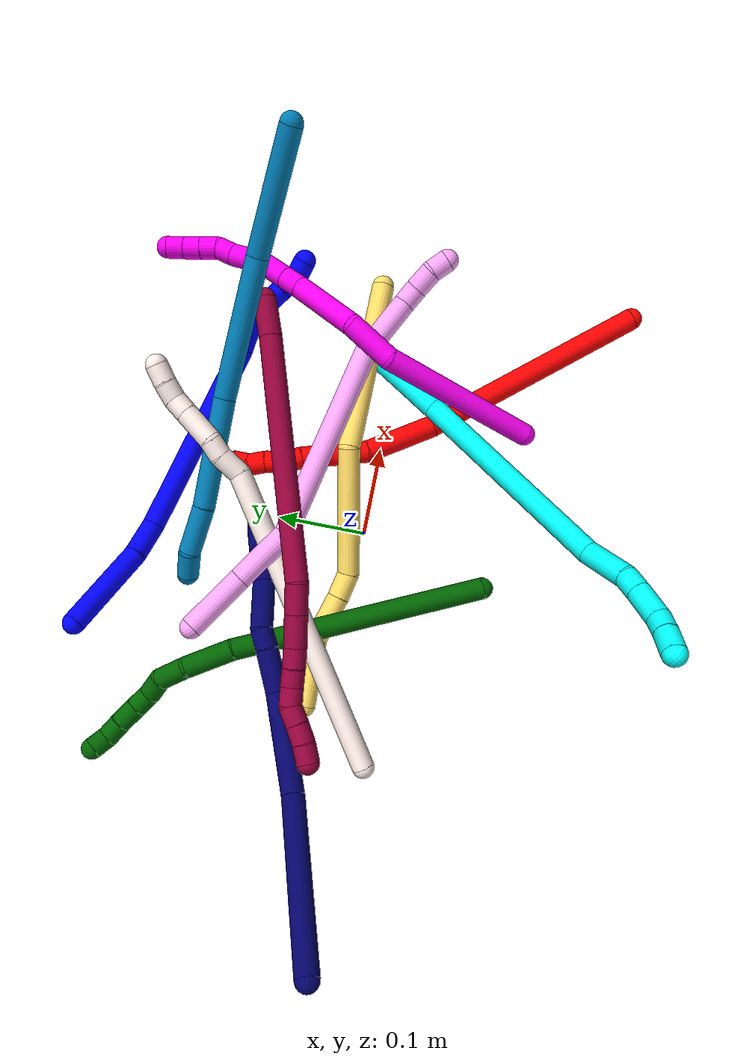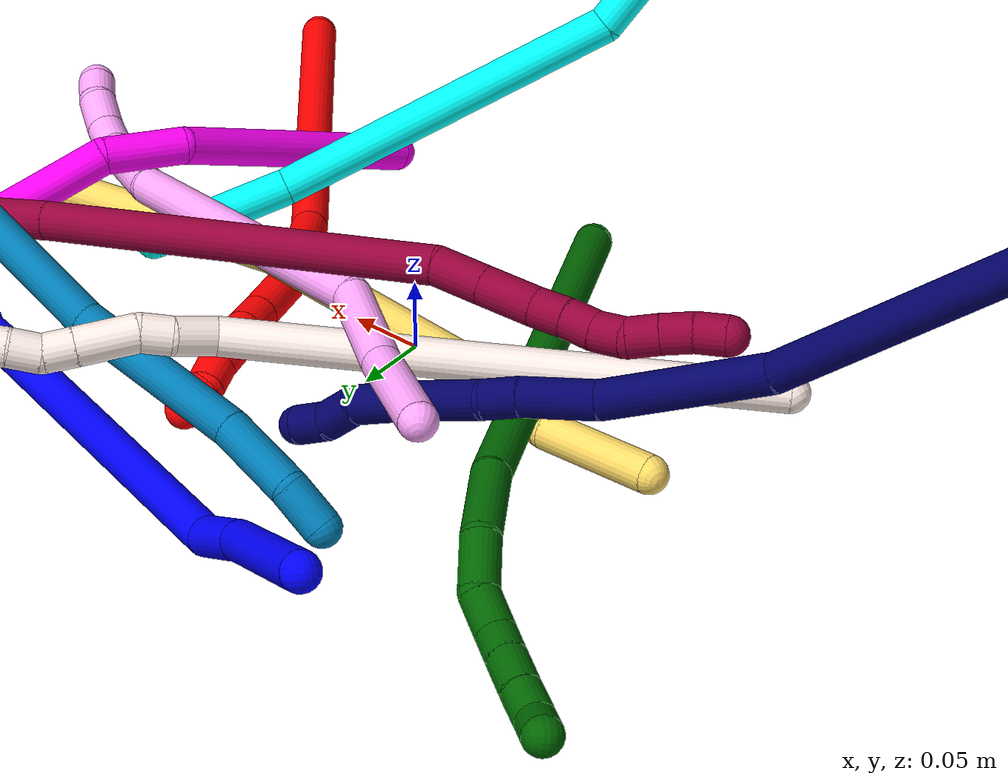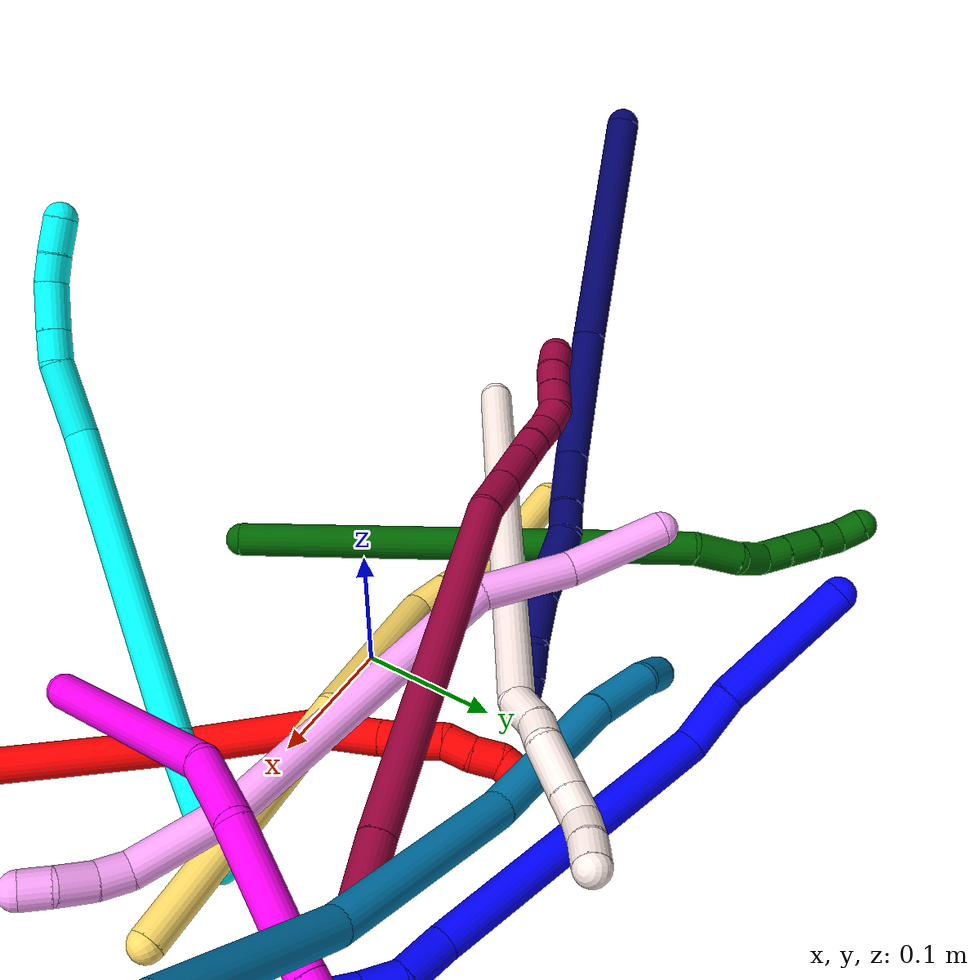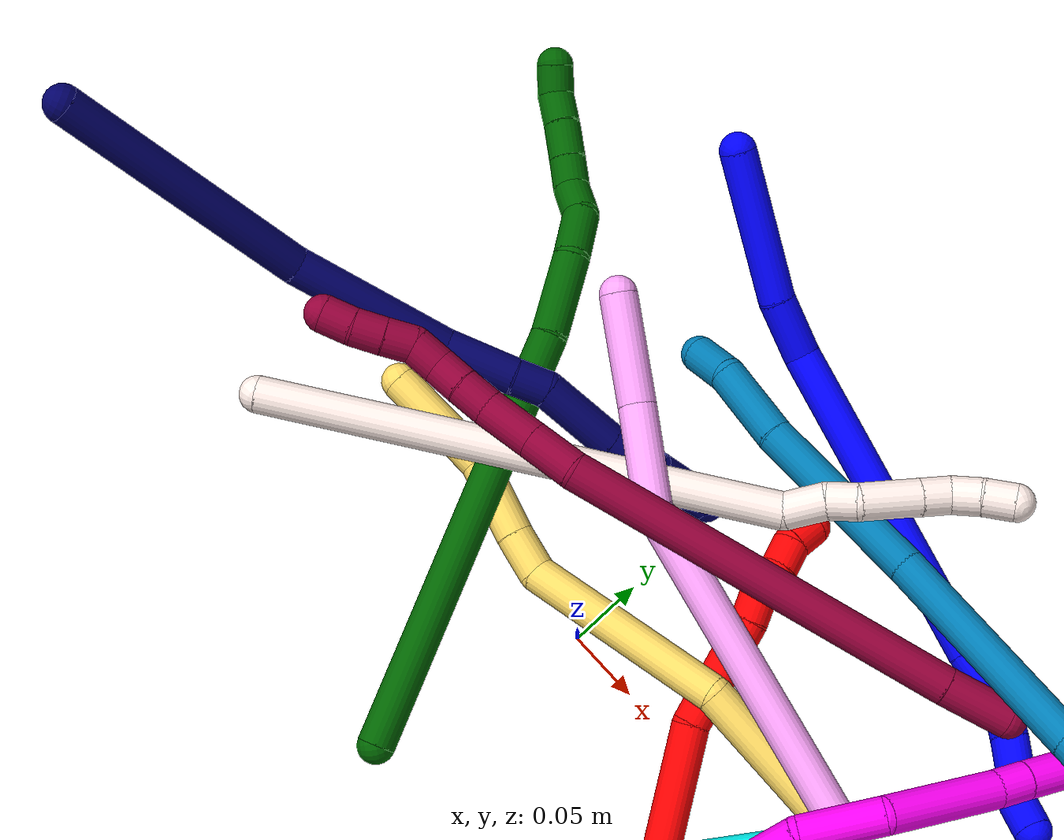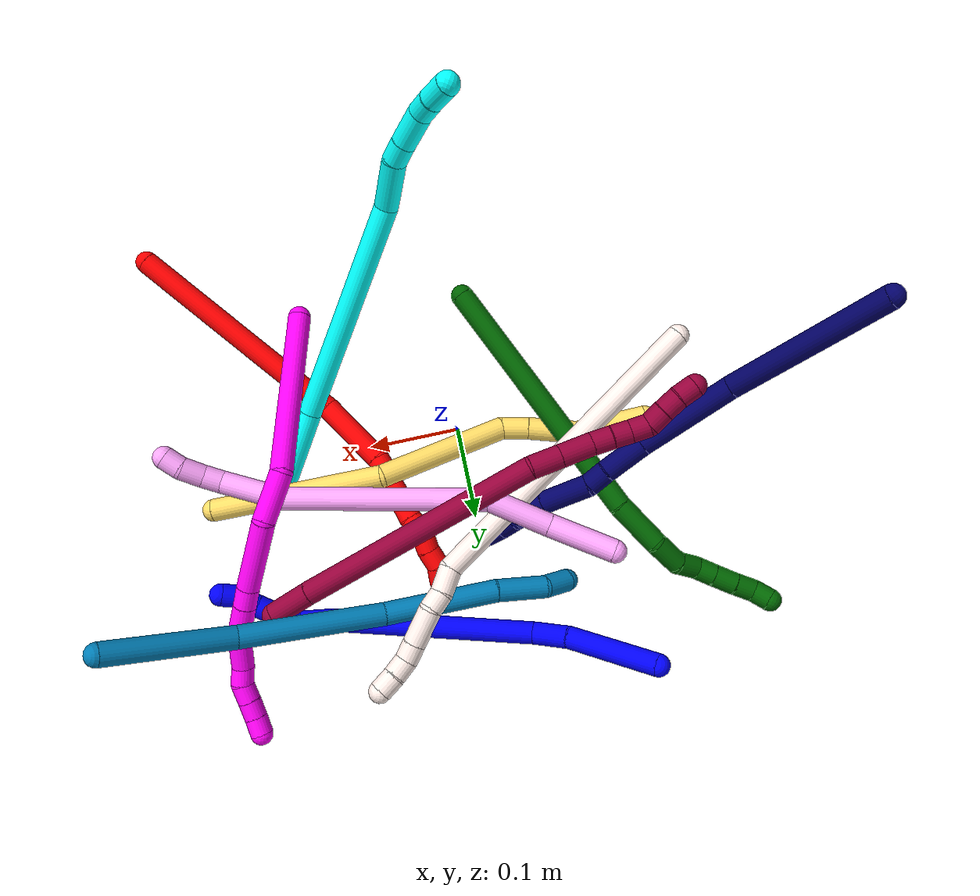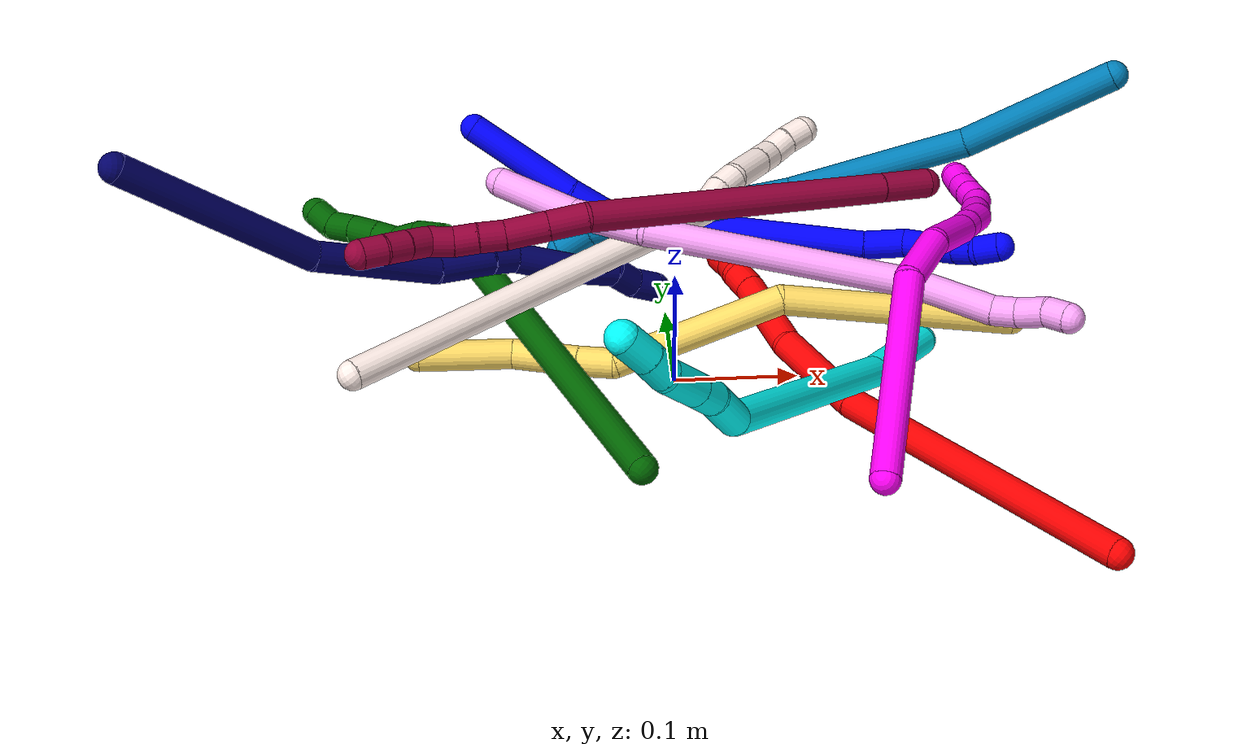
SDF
<sdf version="1.7">
 <world name="default">
  <plugin name="TubeGeneratorPlugin" filename="libtube_generator_plugin.so"/>
  <model name="photoneo_s_sensor">
   <static>1</static>
   <pose>0 0 2 1.57079 1.57079 3.14159</pose>
   <link name="link">
    <inertial><mass>0.1</mass></inertial>
    <sensor name="sensor" type="depth">
     <update_rate>30</update_rate>
     <camera>
      <horizontal_fov>1.22</horizontal_fov>
      <image><width>1920</width><height>1200</height><format>B8G8R8</format></image>
      <clip><near>0.1</near><far>4</far></clip>
      <depth_camera><output>points</output></depth_camera>
     </camera>
     <plugin name="camera_plugin" filename="libgazebo_ros_depth_camera.so">
      <baseline>0.2</baseline>
      <alwaysOn>1</alwaysOn>
      <updateRate>0.0</updateRate>
      <cameraName>camera_ir</cameraName>
      <imageTopicName>/camera/color/image_raw</imageTopicName>
      <cameraInfoTopicName>/camera/color/camera_info</cameraInfoTopicName>
      <depthImageTopicName>/camera/depth/image_raw</depthImageTopicName>
      <depthImageCameraInfoTopicName>/camera/depth/camera_info</depthImageCameraInfoTopicName>
      <pointCloudTopicName>/camera/depth/points</pointCloudTopicName>
      <frameName>fr_optical</frameName>
      <pointCloudCutoff>0.1</pointCloudCutoff>
      <pointCloudCutoffMax>2.0</pointCloudCutoffMax>
      <distortionK1>0</distortionK1>
      <distortionK2>0</distortionK2>
      <distortionK3>0</distortionK3>
      <distortionT1>0</distortionT1>
      <distortionT2>0</distortionT2>
      <CxPrime>0</CxPrime>
      <Cx>0</Cx>
      <Cy>0</Cy>
      <focalLength>0</focalLength>
      <hackBaseline>0</hackBaseline>
     </plugin>
    </sensor>
   </link>
  </model>
  <gravity>0 0 -9.8</gravity>
  <magnetic_field>6e-06 2.3e-05 -4.2e-05</magnetic_field>
  <atmosphere type="adiabatic"/>
  <physics name="default_physics" default="0" type="ode">
   <max_step_size>0.003</max_step_size>
   <real_time_factor>1</real_time_factor>
   <real_time_update_rate>1000</real_time_update_rate>
   <max_contacts>10000</max_contacts>
   <ode>
    <solver>
     <type>quick</type>
     <iters>100</iters>
     <sor>1.3</sor>
     <use_dynamic_moi_rescaling>0</use_dynamic_moi_rescaling>
    </solver>
    <constraints>
     <contact_max_correcting_vel>0</contact_max_correcting_vel>
     <contact_surface_layer>0.001</contact_surface_layer>
     <cfm>0</cfm>
     <erp>0.2</erp>
    </constraints>
   </ode>
  </physics>
  <scene><ambient>0.4 0.4 0.4 1</ambient><background>0.7 0.7 0.7 1</background><shadows>0</shadows></scene>
  <audio><device>default</device></audio>
  <spherical_coordinates>
   <surface_model>EARTH_WGS84</surface_model>
   <latitude_deg>0</latitude_deg>
   <longitude_deg>0</longitude_deg>
   <elevation>0</elevation>
   <heading_deg>0</heading_deg>
  </spherical_coordinates>
  <model name="bin">
   <static>1</static>
   <link name="bottom">
    <collision name="collision-bottom">
     <pose>0 0 -0.01 0 -0 0</pose>
     <geometry><box><size>0.8 0.6 0.02</size></box></geometry>
     <surface>
      <friction><ode><mu>100</mu><mu2>100</mu2></ode></friction>
      <contact><collide_bitmask>65535</collide_bitmask></contact>
     </surface>
    </collision>
   </link>
   <link name="west_wall">
    <collision name="collision-west_wall">
     <pose>-0.41 0 0.1 0 -0 0</pose>
     <geometry><box><size>0.02 0.6 0.2</size></box></geometry>
     <surface>
      <friction><ode><mu>100</mu><mu2>100</mu2></ode></friction>
      <contact><collide_bitmask>65535</collide_bitmask></contact>
     </surface>
    </collision>
   </link>
   <link name="east_wall">
    <collision name="collision-east_wall">
     <pose>0.41 0 0.1 0 -0 0</pose>
     <geometry><box><size>0.02 0.6 0.2</size></box></geometry>
     <surface>
      <friction><ode><mu>100</mu><mu2>100</mu2></ode></friction>
      <contact><collide_bitmask>65535</collide_bitmask></contact>
     </surface>
    </collision>
   </link>
   <link name="south_wall">
    <collision name="collision-south_wall">
     <pose>0 -0.31 0.1 0 -0 0</pose>
     <geometry><box><size>0.8 0.02 0.2</size></box></geometry>
     <surface>
      <friction><ode><mu>100</mu><mu2>100</mu2></ode></friction>
      <contact><collide_bitmask>65535</collide_bitmask></contact>
     </surface>
    </collision>
   </link>
   <link name="north_wall">
    <collision name="collision-north_wall">
     <pose>0 0.31 0.1 0 -0 0</pose>
     <geometry><box><size>0.8 0.02 0.2</size></box></geometry>
     <surface>
      <friction><ode><mu>100</mu><mu2>100</mu2></ode></friction>
      <contact><collide_bitmask>65535</collide_bitmask></contact>
     </surface>
    </collision>
   </link>
  </model>
  <model name="1">
   <static>0</static>
   <link name="1">
    <collision name="collision-cylinder-e_1_1_4">
     <pose>0.050886 -0.006132 -0.006552 2.38928 1.39624 2.26171</pose>
     <geometry><cylinder><radius>0.0125</radius><length>0.103343</length></cylinder></geometry>
     <surface>
      <friction><ode><mu>1.16</mu><mu2>1.16</mu2><slip1>0</slip1><slip2>0</slip2></ode></friction>
      <contact><ode><kp>1e+06</kp><kd>1</kd><max_vel>0</max_vel><min_depth>0.001</min_depth></ode></contact>
     </surface>
    </collision>
    <visual name="visual-cylinder-e_1_1_4">
     <pose>0.050886 -0.006132 -0.006552 2.38928 1.39624 2.26171</pose>
     <geometry><cylinder><radius>0.0125</radius><length>0.103343</length></cylinder></geometry>
     <material><ambient>0 0 1 1</ambient></material>
    </visual>
    <collision name="collision-cylinder-e_2_4_5">
     <pose>0.122388 -0.018203 -0.014218 1.75629 1.28565 1.46845</pose>
     <geometry><cylinder><radius>0.0125</radius><length>0.042965</length></cylinder></geometry>
     <surface>
      <friction><ode><mu>1.16</mu><mu2>1.16</mu2><slip1>0</slip1><slip2>0</slip2></ode></friction>
      <contact><ode><kp>1e+06</kp><kd>1</kd><max_vel>0</max_vel><min_depth>0.001</min_depth></ode></contact>
     </surface>
    </collision>
    <visual name="visual-cylinder-e_2_4_5">
     <pose>0.122388 -0.018203 -0.014218 1.75629 1.28565 1.46845</pose>
     <geometry><cylinder><radius>0.0125</radius><length>0.042965</length></cylinder></geometry>
     <material><ambient>0 0 1 1</ambient></material>
    </visual>
    <collision name="collision-cylinder-e_3_5_6">
     <pose>0.232405 -0.06129 -0.073582 2.57389 0.912888 2.06942</pose>
     <geometry><cylinder><radius>0.0125</radius><length>0.225972</length></cylinder></geometry>
     <surface>
      <friction><ode><mu>1.16</mu><mu2>1.16</mu2><slip1>0</slip1><slip2>0</slip2></ode></friction>
      <contact><ode><kp>1e+06</kp><kd>1</kd><max_vel>0</max_vel><min_depth>0.001</min_depth></ode></contact>
     </surface>
    </collision>
    <visual name="visual-cylinder-e_3_5_6">
     <pose>0.232405 -0.06129 -0.073582 2.57389 0.912888 2.06942</pose>
     <geometry><cylinder><radius>0.0125</radius><length>0.225972</length></cylinder></geometry>
     <material><ambient>0 0 1 1</ambient></material>
    </visual>
    <collision name="collision-cylinder-e_4_6_7">
     <pose>0.334014 -0.10633 -0.142329 2.49698 0.748832 1.73278</pose>
     <geometry><cylinder><radius>0.0125</radius><length>0.035859</length></cylinder></geometry>
     <surface>
      <friction><ode><mu>1.16</mu><mu2>1.16</mu2><slip1>0</slip1><slip2>0</slip2></ode></friction>
      <contact><ode><kp>1e+06</kp><kd>1</kd><max_vel>0</max_vel><min_depth>0.001</min_depth></ode></contact>
     </surface>
    </collision>
    <visual name="visual-cylinder-e_4_6_7">
     <pose>0.334014 -0.10633 -0.142329 2.49698 0.748832 1.73278</pose>
     <geometry><cylinder><radius>0.0125</radius><length>0.035859</length></cylinder></geometry>
     <material><ambient>0 0 1 1</ambient></material>
    </visual>
    <collision name="collision-cylinder-e_5_7_8">
     <pose>0.356217 -0.114599 -0.162164 3.10118 0.819146 3.04856</pose>
     <geometry><cylinder><radius>0.0125</radius><length>0.027368</length></cylinder></geometry>
     <surface>
      <friction><ode><mu>1.16</mu><mu2>1.16</mu2><slip1>0</slip1><slip2>0</slip2></ode></friction>
      <contact><ode><kp>1e+06</kp><kd>1</kd><max_vel>0</max_vel><min_depth>0.001</min_depth></ode></contact>
     </surface>
    </collision>
    <visual name="visual-cylinder-e_5_7_8">
     <pose>0.356217 -0.114599 -0.162164 3.10118 0.819146 3.04856</pose>
     <geometry><cylinder><radius>0.0125</radius><length>0.027368</length></cylinder></geometry>
     <material><ambient>0 0 1 1</ambient></material>
    </visual>
    <collision name="collision-cylinder-e_6_8_9">
     <pose>0.374234 -0.11454 -0.180093 -3.09091 0.750272 -3.01303</pose>
     <geometry><cylinder><radius>0.0125</radius><length>0.023523</length></cylinder></geometry>
     <surface>
      <friction><ode><mu>1.16</mu><mu2>1.16</mu2><slip1>0</slip1><slip2>0</slip2></ode></friction>
      <contact><ode><kp>1e+06</kp><kd>1</kd><max_vel>0</max_vel><min_depth>0.001</min_depth></ode></contact>
     </surface>
    </collision>
    <visual name="visual-cylinder-e_6_8_9">
     <pose>0.374234 -0.11454 -0.180093 -3.09091 0.750272 -3.01303</pose>
     <geometry><cylinder><radius>0.0125</radius><length>0.023523</length></cylinder></geometry>
     <material><ambient>0 0 1 1</ambient></material>
    </visual>
    <collision name="collision-cylinder-e_7_9_10">
     <pose>0.387843 -0.112558 -0.196939 -2.95643 0.58727 -2.54576</pose>
     <geometry><cylinder><radius>0.0125</radius><length>0.020176</length></cylinder></geometry>
     <surface>
      <friction><ode><mu>1.16</mu><mu2>1.16</mu2><slip1>0</slip1><slip2>0</slip2></ode></friction>
      <contact><ode><kp>1e+06</kp><kd>1</kd><max_vel>0</max_vel><min_depth>0.001</min_depth></ode></contact>
     </surface>
    </collision>
    <visual name="visual-cylinder-e_7_9_10">
     <pose>0.387843 -0.112558 -0.196939 -2.95643 0.58727 -2.54576</pose>
     <geometry><cylinder><radius>0.0125</radius><length>0.020176</length></cylinder></geometry>
     <material><ambient>0 0 1 1</ambient></material>
    </visual>
    <collision name="collision-cylinder-e_8_10_2">
     <pose>0.399282 -0.113711 -0.213355 2.82218 0.597482 2.17775</pose>
     <geometry><cylinder><radius>0.0125</radius><length>0.020794</length></cylinder></geometry>
     <surface>
      <friction><ode><mu>1.16</mu><mu2>1.16</mu2><slip1>0</slip1><slip2>0</slip2></ode></friction>
      <contact><ode><kp>1e+06</kp><kd>1</kd><max_vel>0</max_vel><min_depth>0.001</min_depth></ode></contact>
     </surface>
    </collision>
    <visual name="visual-cylinder-e_8_10_2">
     <pose>0.399282 -0.113711 -0.213355 2.82218 0.597482 2.17775</pose>
     <geometry><cylinder><radius>0.0125</radius><length>0.020794</length></cylinder></geometry>
     <material><ambient>0 0 1 1</ambient></material>
    </visual>
    <collision name="collision-sphere-2">
     <pose>0.405131 -0.116411 -0.221516 0 -0 0</pose>
     <geometry><sphere><radius>0.0125</radius></sphere></geometry>
     <surface>
      <friction><ode><mu>1.16</mu><mu2>1.16</mu2><slip1>0</slip1><slip2>0</slip2></ode></friction>
      <contact><ode><kp>1e+06</kp><kd>1</kd><max_vel>0</max_vel><min_depth>0.001</min_depth></ode></contact>
     </surface>
    </collision>
    <visual name="visual-sphere-2">
     <pose>0.405131 -0.116411 -0.221516 0 -0 0</pose>
     <geometry><sphere><radius>0.0125</radius></sphere></geometry>
     <material><ambient>0 0 1 1</ambient></material>
    </visual>
    <collision name="collision-sphere-10">
     <pose>0.393432 -0.111012 -0.205194 0 -0 0</pose>
     <geometry><sphere><radius>0.0125</radius></sphere></geometry>
     <surface>
      <friction><ode><mu>1.16</mu><mu2>1.16</mu2><slip1>0</slip1><slip2>0</slip2></ode></friction>
      <contact><ode><kp>1e+06</kp><kd>1</kd><max_vel>0</max_vel><min_depth>0.001</min_depth></ode></contact>
     </surface>
    </collision>
    <visual name="visual-sphere-10">
     <pose>0.393432 -0.111012 -0.205194 0 -0 0</pose>
     <geometry><sphere><radius>0.0125</radius></sphere></geometry>
     <material><ambient>0 0 1 1</ambient></material>
    </visual>
    <collision name="collision-sphere-9">
     <pose>0.382253 -0.114104 -0.188685 0 -0 0</pose>
     <geometry><sphere><radius>0.0125</radius></sphere></geometry>
     <surface>
      <friction><ode><mu>1.16</mu><mu2>1.16</mu2><slip1>0</slip1><slip2>0</slip2></ode></friction>
      <contact><ode><kp>1e+06</kp><kd>1</kd><max_vel>0</max_vel><min_depth>0.001</min_depth></ode></contact>
     </surface>
    </collision>
    <visual name="visual-sphere-9">
     <pose>0.382253 -0.114104 -0.188685 0 -0 0</pose>
     <geometry><sphere><radius>0.0125</radius></sphere></geometry>
     <material><ambient>0 0 1 1</ambient></material>
    </visual>
    <collision name="collision-sphere-4">
     <pose>0.101773 -0.012264 -0.013104 0 -0 0</pose>
     <geometry><sphere><radius>0.0125</radius></sphere></geometry>
     <surface>
      <friction><ode><mu>1.16</mu><mu2>1.16</mu2><slip1>0</slip1><slip2>0</slip2></ode></friction>
      <contact><ode><kp>1e+06</kp><kd>1</kd><max_vel>0</max_vel><min_depth>0.001</min_depth></ode></contact>
     </surface>
    </collision>
    <visual name="visual-sphere-4">
     <pose>0.101773 -0.012264 -0.013104 0 -0 0</pose>
     <geometry><sphere><radius>0.0125</radius></sphere></geometry>
     <material><ambient>0 0 1 1</ambient></material>
    </visual>
    <collision name="collision-sphere-1">
     <geometry><sphere><radius>0.0125</radius></sphere></geometry>
     <surface>
      <friction><ode><mu>1.16</mu><mu2>1.16</mu2><slip1>0</slip1><slip2>0</slip2></ode></friction>
      <contact><ode><kp>1e+06</kp><kd>1</kd><max_vel>0</max_vel><min_depth>0.001</min_depth></ode></contact>
     </surface>
    </collision>
    <visual name="visual-sphere-1">
     <geometry><sphere><radius>0.0125</radius></sphere></geometry>
     <material><ambient>0 0 1 1</ambient></material>
    </visual>
    <collision name="collision-sphere-8">
     <pose>0.366214 -0.114976 -0.1715 0 -0 0</pose>
     <geometry><sphere><radius>0.0125</radius></sphere></geometry>
     <surface>
      <friction><ode><mu>1.16</mu><mu2>1.16</mu2><slip1>0</slip1><slip2>0</slip2></ode></friction>
      <contact><ode><kp>1e+06</kp><kd>1</kd><max_vel>0</max_vel><min_depth>0.001</min_depth></ode></contact>
     </surface>
    </collision>
    <visual name="visual-sphere-8">
     <pose>0.366214 -0.114976 -0.1715 0 -0 0</pose>
     <geometry><sphere><radius>0.0125</radius></sphere></geometry>
     <material><ambient>0 0 1 1</ambient></material>
    </visual>
    <collision name="collision-sphere-5">
     <pose>0.143003 -0.024143 -0.015333 0 -0 0</pose>
     <geometry><sphere><radius>0.0125</radius></sphere></geometry>
     <surface>
      <friction><ode><mu>1.16</mu><mu2>1.16</mu2><slip1>0</slip1><slip2>0</slip2></ode></friction>
      <contact><ode><kp>1e+06</kp><kd>1</kd><max_vel>0</max_vel><min_depth>0.001</min_depth></ode></contact>
     </surface>
    </collision>
    <visual name="visual-sphere-5">
     <pose>0.143003 -0.024143 -0.015333 0 -0 0</pose>
     <geometry><sphere><radius>0.0125</radius></sphere></geometry>
     <material><ambient>0 0 1 1</ambient></material>
    </visual>
    <collision name="collision-sphere-6">
     <pose>0.321808 -0.098438 -0.131832 0 -0 0</pose>
     <geometry><sphere><radius>0.0125</radius></sphere></geometry>
     <surface>
      <friction><ode><mu>1.16</mu><mu2>1.16</mu2><slip1>0</slip1><slip2>0</slip2></ode></friction>
      <contact><ode><kp>1e+06</kp><kd>1</kd><max_vel>0</max_vel><min_depth>0.001</min_depth></ode></contact>
     </surface>
    </collision>
    <visual name="visual-sphere-6">
     <pose>0.321808 -0.098438 -0.131832 0 -0 0</pose>
     <geometry><sphere><radius>0.0125</radius></sphere></geometry>
     <material><ambient>0 0 1 1</ambient></material>
    </visual>
    <collision name="collision-sphere-7">
     <pose>0.34622 -0.114221 -0.152827 0 -0 0</pose>
     <geometry><sphere><radius>0.0125</radius></sphere></geometry>
     <surface>
      <friction><ode><mu>1.16</mu><mu2>1.16</mu2><slip1>0</slip1><slip2>0</slip2></ode></friction>
      <contact><ode><kp>1e+06</kp><kd>1</kd><max_vel>0</max_vel><min_depth>0.001</min_depth></ode></contact>
     </surface>
    </collision>
    <visual name="visual-sphere-7">
     <pose>0.34622 -0.114221 -0.152827 0 -0 0</pose>
     <geometry><sphere><radius>0.0125</radius></sphere></geometry>
     <material><ambient>0 0 1 1</ambient></material>
    </visual>
    <inertial>
     <pose>0.219383 -0.05909 -0.080207 0 -0 0</pose>
     <mass>0.5</mass>
     <inertia>
      <ixx>0.000272</ixx>
      <ixy>0</ixy>
      <ixz>0</ixz>
      <iyy>0.001397</iyy>
      <iyz>0</iyz>
      <izz>-0.000561</izz>
     </inertia>
    </inertial>
   </link>
   <pose>-0.157883 0.287241 0.081157 -3.07738 0.605098 -0.563404</pose>
  </model>
  <model name="2">
   <static>0</static>
   <link name="2">
    <collision name="collision-cylinder-e_1_1_4">
     <pose>-0.038239 0.066086 -0.106243 -2.58513 -0.296604 0.96381</pose>
     <geometry><cylinder><radius>0.0125</radius><length>0.261666</length></cylinder></geometry>
     <surface>
      <friction><ode><mu>1.16</mu><mu2>1.16</mu2><slip1>0</slip1><slip2>0</slip2></ode></friction>
      <contact><ode><kp>1e+06</kp><kd>1</kd><max_vel>0</max_vel><min_depth>0.001</min_depth></ode></contact>
     </surface>
    </collision>
    <visual name="visual-cylinder-e_1_1_4">
     <pose>-0.038239 0.066086 -0.106243 -2.58513 -0.296604 0.96381</pose>
     <geometry><cylinder><radius>0.0125</radius><length>0.261666</length></cylinder></geometry>
     <material><ambient>1 0 0 1</ambient></material>
    </visual>
    <collision name="collision-cylinder-e_2_4_5">
     <pose>-0.092479 0.145703 -0.247485 -2.7727 -0.403086 1.66155</pose>
     <geometry><cylinder><radius>0.0125</radius><length>0.081585</length></cylinder></geometry>
     <surface>
      <friction><ode><mu>1.16</mu><mu2>1.16</mu2><slip1>0</slip1><slip2>0</slip2></ode></friction>
      <contact><ode><kp>1e+06</kp><kd>1</kd><max_vel>0</max_vel><min_depth>0.001</min_depth></ode></contact>
     </surface>
    </collision>
    <visual name="visual-cylinder-e_2_4_5">
     <pose>-0.092479 0.145703 -0.247485 -2.7727 -0.403086 1.66155</pose>
     <geometry><cylinder><radius>0.0125</radius><length>0.081585</length></cylinder></geometry>
     <material><ambient>1 0 0 1</ambient></material>
    </visual>
    <collision name="collision-cylinder-e_3_5_6">
     <pose>-0.125262 0.168226 -0.300786 -2.6849 -0.688588 1.99148</pose>
     <geometry><cylinder><radius>0.0125</radius><length>0.052819</length></cylinder></geometry>
     <surface>
      <friction><ode><mu>1.16</mu><mu2>1.16</mu2><slip1>0</slip1><slip2>0</slip2></ode></friction>
      <contact><ode><kp>1e+06</kp><kd>1</kd><max_vel>0</max_vel><min_depth>0.001</min_depth></ode></contact>
     </surface>
    </collision>
    <visual name="visual-cylinder-e_3_5_6">
     <pose>-0.125262 0.168226 -0.300786 -2.6849 -0.688588 1.99148</pose>
     <geometry><cylinder><radius>0.0125</radius><length>0.052819</length></cylinder></geometry>
     <material><ambient>1 0 0 1</ambient></material>
    </visual>
    <collision name="collision-cylinder-e_4_6_7">
     <pose>-0.149439 0.180814 -0.327362 -2.73158 -0.686654 2.08797</pose>
     <geometry><cylinder><radius>0.0125</radius><length>0.023329</length></cylinder></geometry>
     <surface>
      <friction><ode><mu>1.16</mu><mu2>1.16</mu2><slip1>0</slip1><slip2>0</slip2></ode></friction>
      <contact><ode><kp>1e+06</kp><kd>1</kd><max_vel>0</max_vel><min_depth>0.001</min_depth></ode></contact>
     </surface>
    </collision>
    <visual name="visual-cylinder-e_4_6_7">
     <pose>-0.149439 0.180814 -0.327362 -2.73158 -0.686654 2.08797</pose>
     <geometry><cylinder><radius>0.0125</radius><length>0.023329</length></cylinder></geometry>
     <material><ambient>1 0 0 1</ambient></material>
    </visual>
    <collision name="collision-cylinder-e_5_7_8">
     <pose>-0.161943 0.188079 -0.343679 -2.71372 -0.524039 1.77984</pose>
     <geometry><cylinder><radius>0.0125</radius><length>0.020422</length></cylinder></geometry>
     <surface>
      <friction><ode><mu>1.16</mu><mu2>1.16</mu2><slip1>0</slip1><slip2>0</slip2></ode></friction>
      <contact><ode><kp>1e+06</kp><kd>1</kd><max_vel>0</max_vel><min_depth>0.001</min_depth></ode></contact>
     </surface>
    </collision>
    <visual name="visual-cylinder-e_5_7_8">
     <pose>-0.161943 0.188079 -0.343679 -2.71372 -0.524039 1.77984</pose>
     <geometry><cylinder><radius>0.0125</radius><length>0.020422</length></cylinder></geometry>
     <material><ambient>1 0 0 1</ambient></material>
    </visual>
    <collision name="collision-cylinder-e_6_8_9">
     <pose>-0.174393 0.19704 -0.356152 -2.26762 -0.816232 1.49365</pose>
     <geometry><cylinder><radius>0.0125</radius><length>0.02015</length></cylinder></geometry>
     <surface>
      <friction><ode><mu>1.16</mu><mu2>1.16</mu2><slip1>0</slip1><slip2>0</slip2></ode></friction>
      <contact><ode><kp>1e+06</kp><kd>1</kd><max_vel>0</max_vel><min_depth>0.001</min_depth></ode></contact>
     </surface>
    </collision>
    <visual name="visual-cylinder-e_6_8_9">
     <pose>-0.174393 0.19704 -0.356152 -2.26762 -0.816232 1.49365</pose>
     <geometry><cylinder><radius>0.0125</radius><length>0.02015</length></cylinder></geometry>
     <material><ambient>1 0 0 1</ambient></material>
    </visual>
    <collision name="collision-cylinder-e_7_9_10">
     <pose>-0.187481 0.207984 -0.366501 -2.37936 -0.612196 1.3356</pose>
     <geometry><cylinder><radius>0.0125</radius><length>0.020002</length></cylinder></geometry>
     <surface>
      <friction><ode><mu>1.16</mu><mu2>1.16</mu2><slip1>0</slip1><slip2>0</slip2></ode></friction>
      <contact><ode><kp>1e+06</kp><kd>1</kd><max_vel>0</max_vel><min_depth>0.001</min_depth></ode></contact>
     </surface>
    </collision>
    <visual name="visual-cylinder-e_7_9_10">
     <pose>-0.187481 0.207984 -0.366501 -2.37936 -0.612196 1.3356</pose>
     <geometry><cylinder><radius>0.0125</radius><length>0.020002</length></cylinder></geometry>
     <material><ambient>1 0 0 1</ambient></material>
    </visual>
    <collision name="collision-cylinder-e_8_10_2">
     <pose>-0.200952 0.219665 -0.374482 -1.90019 -0.881034 1.16583</pose>
     <geometry><cylinder><radius>0.0125</radius><length>0.020027</length></cylinder></geometry>
     <surface>
      <friction><ode><mu>1.16</mu><mu2>1.16</mu2><slip1>0</slip1><slip2>0</slip2></ode></friction>
      <contact><ode><kp>1e+06</kp><kd>1</kd><max_vel>0</max_vel><min_depth>0.001</min_depth></ode></contact>
     </surface>
    </collision>
    <visual name="visual-cylinder-e_8_10_2">
     <pose>-0.200952 0.219665 -0.374482 -1.90019 -0.881034 1.16583</pose>
     <geometry><cylinder><radius>0.0125</radius><length>0.020027</length></cylinder></geometry>
     <material><ambient>1 0 0 1</ambient></material>
    </visual>
    <collision name="collision-sphere-2">
     <pose>-0.208677 0.225695 -0.376543 0 -0 0</pose>
     <geometry><sphere><radius>0.0125</radius></sphere></geometry>
     <surface>
      <friction><ode><mu>1.16</mu><mu2>1.16</mu2><slip1>0</slip1><slip2>0</slip2></ode></friction>
      <contact><ode><kp>1e+06</kp><kd>1</kd><max_vel>0</max_vel><min_depth>0.001</min_depth></ode></contact>
     </surface>
    </collision>
    <visual name="visual-sphere-2">
     <pose>-0.208677 0.225695 -0.376543 0 -0 0</pose>
     <geometry><sphere><radius>0.0125</radius></sphere></geometry>
     <material><ambient>1 0 0 1</ambient></material>
    </visual>
    <collision name="collision-sphere-10">
     <pose>-0.193228 0.213636 -0.372421 0 -0 0</pose>
     <geometry><sphere><radius>0.0125</radius></sphere></geometry>
     <surface>
      <friction><ode><mu>1.16</mu><mu2>1.16</mu2><slip1>0</slip1><slip2>0</slip2></ode></friction>
      <contact><ode><kp>1e+06</kp><kd>1</kd><max_vel>0</max_vel><min_depth>0.001</min_depth></ode></contact>
     </surface>
    </collision>
    <visual name="visual-sphere-10">
     <pose>-0.193228 0.213636 -0.372421 0 -0 0</pose>
     <geometry><sphere><radius>0.0125</radius></sphere></geometry>
     <material><ambient>1 0 0 1</ambient></material>
    </visual>
    <collision name="collision-sphere-9">
     <pose>-0.181734 0.202332 -0.360581 0 -0 0</pose>
     <geometry><sphere><radius>0.0125</radius></sphere></geometry>
     <surface>
      <friction><ode><mu>1.16</mu><mu2>1.16</mu2><slip1>0</slip1><slip2>0</slip2></ode></friction>
      <contact><ode><kp>1e+06</kp><kd>1</kd><max_vel>0</max_vel><min_depth>0.001</min_depth></ode></contact>
     </surface>
    </collision>
    <visual name="visual-sphere-9">
     <pose>-0.181734 0.202332 -0.360581 0 -0 0</pose>
     <geometry><sphere><radius>0.0125</radius></sphere></geometry>
     <material><ambient>1 0 0 1</ambient></material>
    </visual>
    <collision name="collision-sphere-4">
     <pose>-0.076478 0.132173 -0.212487 0 -0 0</pose>
     <geometry><sphere><radius>0.0125</radius></sphere></geometry>
     <surface>
      <friction><ode><mu>1.16</mu><mu2>1.16</mu2><slip1>0</slip1><slip2>0</slip2></ode></friction>
      <contact><ode><kp>1e+06</kp><kd>1</kd><max_vel>0</max_vel><min_depth>0.001</min_depth></ode></contact>
     </surface>
    </collision>
    <visual name="visual-sphere-4">
     <pose>-0.076478 0.132173 -0.212487 0 -0 0</pose>
     <geometry><sphere><radius>0.0125</radius></sphere></geometry>
     <material><ambient>1 0 0 1</ambient></material>
    </visual>
    <collision name="collision-sphere-1">
     <geometry><sphere><radius>0.0125</radius></sphere></geometry>
     <surface>
      <friction><ode><mu>1.16</mu><mu2>1.16</mu2><slip1>0</slip1><slip2>0</slip2></ode></friction>
      <contact><ode><kp>1e+06</kp><kd>1</kd><max_vel>0</max_vel><min_depth>0.001</min_depth></ode></contact>
     </surface>
    </collision>
    <visual name="visual-sphere-1">
     <geometry><sphere><radius>0.0125</radius></sphere></geometry>
     <material><ambient>1 0 0 1</ambient></material>
    </visual>
    <collision name="collision-sphere-8">
     <pose>-0.167053 0.191747 -0.351723 0 -0 0</pose>
     <geometry><sphere><radius>0.0125</radius></sphere></geometry>
     <surface>
      <friction><ode><mu>1.16</mu><mu2>1.16</mu2><slip1>0</slip1><slip2>0</slip2></ode></friction>
      <contact><ode><kp>1e+06</kp><kd>1</kd><max_vel>0</max_vel><min_depth>0.001</min_depth></ode></contact>
     </surface>
    </collision>
    <visual name="visual-sphere-8">
     <pose>-0.167053 0.191747 -0.351723 0 -0 0</pose>
     <geometry><sphere><radius>0.0125</radius></sphere></geometry>
     <material><ambient>1 0 0 1</ambient></material>
    </visual>
    <collision name="collision-sphere-5">
     <pose>-0.10848 0.159233 -0.282484 0 -0 0</pose>
     <geometry><sphere><radius>0.0125</radius></sphere></geometry>
     <surface>
      <friction><ode><mu>1.16</mu><mu2>1.16</mu2><slip1>0</slip1><slip2>0</slip2></ode></friction>
      <contact><ode><kp>1e+06</kp><kd>1</kd><max_vel>0</max_vel><min_depth>0.001</min_depth></ode></contact>
     </surface>
    </collision>
    <visual name="visual-sphere-5">
     <pose>-0.10848 0.159233 -0.282484 0 -0 0</pose>
     <geometry><sphere><radius>0.0125</radius></sphere></geometry>
     <material><ambient>1 0 0 1</ambient></material>
    </visual>
    <collision name="collision-sphere-6">
     <pose>-0.142044 0.177218 -0.319088 0 -0 0</pose>
     <geometry><sphere><radius>0.0125</radius></sphere></geometry>
     <surface>
      <friction><ode><mu>1.16</mu><mu2>1.16</mu2><slip1>0</slip1><slip2>0</slip2></ode></friction>
      <contact><ode><kp>1e+06</kp><kd>1</kd><max_vel>0</max_vel><min_depth>0.001</min_depth></ode></contact>
     </surface>
    </collision>
    <visual name="visual-sphere-6">
     <pose>-0.142044 0.177218 -0.319088 0 -0 0</pose>
     <geometry><sphere><radius>0.0125</radius></sphere></geometry>
     <material><ambient>1 0 0 1</ambient></material>
    </visual>
    <collision name="collision-sphere-7">
     <pose>-0.156834 0.18441 -0.335635 0 -0 0</pose>
     <geometry><sphere><radius>0.0125</radius></sphere></geometry>
     <surface>
      <friction><ode><mu>1.16</mu><mu2>1.16</mu2><slip1>0</slip1><slip2>0</slip2></ode></friction>
      <contact><ode><kp>1e+06</kp><kd>1</kd><max_vel>0</max_vel><min_depth>0.001</min_depth></ode></contact>
     </surface>
    </collision>
    <visual name="visual-sphere-7">
     <pose>-0.156834 0.18441 -0.335635 0 -0 0</pose>
     <geometry><sphere><radius>0.0125</radius></sphere></geometry>
     <material><ambient>1 0 0 1</ambient></material>
    </visual>
    <inertial>
     <pose>-0.084498 0.117308 -0.201082 0 -0 0</pose>
     <mass>0.5</mass>
     <inertia>
      <ixx>0.002036</ixx>
      <ixy>0</ixy>
      <ixz>0</ixz>
      <iyy>0.000745</iyy>
      <iyz>0</iyz>
      <izz>-0.000341</izz>
     </inertia>
    </inertial>
   </link>
   <pose>0.304371 -0.25389 0.009954 -2.10387 0.059486 -2.1515</pose>
  </model>
  <model name="3">
   <static>0</static>
   <link name="3">
    <collision name="collision-cylinder-e_1_1_4">
     <pose>-0.004735 -0.011561 0.046551 0.24342 -0.098401 -0.012045</pose>
     <geometry><cylinder><radius>0.0125</radius><length>0.096397</length></cylinder></geometry>
     <surface>
      <friction><ode><mu>1.16</mu><mu2>1.16</mu2><slip1>0</slip1><slip2>0</slip2></ode></friction>
      <contact><ode><kp>1e+06</kp><kd>1</kd><max_vel>0</max_vel><min_depth>0.001</min_depth></ode></contact>
     </surface>
    </collision>
    <visual name="visual-cylinder-e_1_1_4">
     <pose>-0.004735 -0.011561 0.046551 0.24342 -0.098401 -0.012045</pose>
     <geometry><cylinder><radius>0.0125</radius><length>0.096397</length></cylinder></geometry>
     <material><ambient>0.003922 1 0.996078 1</ambient></material>
    </visual>
    <collision name="collision-cylinder-e_2_4_5">
     <pose>-0.025129 -0.06675 0.204724 0.372602 -0.129925 -0.024522</pose>
     <geometry><cylinder><radius>0.0125</radius><length>0.241728</length></cylinder></geometry>
     <surface>
      <friction><ode><mu>1.16</mu><mu2>1.16</mu2><slip1>0</slip1><slip2>0</slip2></ode></friction>
      <contact><ode><kp>1e+06</kp><kd>1</kd><max_vel>0</max_vel><min_depth>0.001</min_depth></ode></contact>
     </surface>
    </collision>
    <visual name="visual-cylinder-e_2_4_5">
     <pose>-0.025129 -0.06675 0.204724 0.372602 -0.129925 -0.024522</pose>
     <geometry><cylinder><radius>0.0125</radius><length>0.241728</length></cylinder></geometry>
     <material><ambient>0.003922 1 0.996078 1</ambient></material>
    </visual>
    <collision name="collision-cylinder-e_3_5_6">
     <pose>-0.05142 -0.128185 0.33472 0.769722 -0.393794 -0.161254</pose>
     <geometry><cylinder><radius>0.0125</radius><length>0.055415</length></cylinder></geometry>
     <surface>
      <friction><ode><mu>1.16</mu><mu2>1.16</mu2><slip1>0</slip1><slip2>0</slip2></ode></friction>
      <contact><ode><kp>1e+06</kp><kd>1</kd><max_vel>0</max_vel><min_depth>0.001</min_depth></ode></contact>
     </surface>
    </collision>
    <visual name="visual-cylinder-e_3_5_6">
     <pose>-0.05142 -0.128185 0.33472 0.769722 -0.393794 -0.161254</pose>
     <geometry><cylinder><radius>0.0125</radius><length>0.055415</length></cylinder></geometry>
     <material><ambient>0.003922 1 0.996078 1</ambient></material>
    </visual>
    <collision name="collision-cylinder-e_4_6_7">
     <pose>-0.063562 -0.15397 0.36103 0.788103 -0.133509 -0.055581</pose>
     <geometry><cylinder><radius>0.0125</radius><length>0.022708</length></cylinder></geometry>
     <surface>
      <friction><ode><mu>1.16</mu><mu2>1.16</mu2><slip1>0</slip1><slip2>0</slip2></ode></friction>
      <contact><ode><kp>1e+06</kp><kd>1</kd><max_vel>0</max_vel><min_depth>0.001</min_depth></ode></contact>
     </surface>
    </collision>
    <visual name="visual-cylinder-e_4_6_7">
     <pose>-0.063562 -0.15397 0.36103 0.788103 -0.133509 -0.055581</pose>
     <geometry><cylinder><radius>0.0125</radius><length>0.022708</length></cylinder></geometry>
     <material><ambient>0.003922 1 0.996078 1</ambient></material>
    </visual>
    <collision name="collision-cylinder-e_5_7_8">
     <pose>-0.066906 -0.174847 0.381617 0.795002 -0.10105 -0.042456</pose>
     <geometry><cylinder><radius>0.0125</radius><length>0.03632</length></cylinder></geometry>
     <surface>
      <friction><ode><mu>1.16</mu><mu2>1.16</mu2><slip1>0</slip1><slip2>0</slip2></ode></friction>
      <contact><ode><kp>1e+06</kp><kd>1</kd><max_vel>0</max_vel><min_depth>0.001</min_depth></ode></contact>
     </surface>
    </collision>
    <visual name="visual-cylinder-e_5_7_8">
     <pose>-0.066906 -0.174847 0.381617 0.795002 -0.10105 -0.042456</pose>
     <geometry><cylinder><radius>0.0125</radius><length>0.03632</length></cylinder></geometry>
     <material><ambient>0.003922 1 0.996078 1</ambient></material>
    </visual>
    <collision name="collision-cylinder-e_6_8_9">
     <pose>-0.069362 -0.19714 0.399209 1.08679 -0.058777 -0.035511</pose>
     <geometry><cylinder><radius>0.0125</radius><length>0.021266</length></cylinder></geometry>
     <surface>
      <friction><ode><mu>1.16</mu><mu2>1.16</mu2><slip1>0</slip1><slip2>0</slip2></ode></friction>
      <contact><ode><kp>1e+06</kp><kd>1</kd><max_vel>0</max_vel><min_depth>0.001</min_depth></ode></contact>
     </surface>
    </collision>
    <visual name="visual-cylinder-e_6_8_9">
     <pose>-0.069362 -0.19714 0.399209 1.08679 -0.058777 -0.035511</pose>
     <geometry><cylinder><radius>0.0125</radius><length>0.021266</length></cylinder></geometry>
     <material><ambient>0.003922 1 0.996078 1</ambient></material>
    </visual>
    <collision name="collision-cylinder-e_7_9_2">
     <pose>-0.069726 -0.217957 0.410523 1.06174 0.019898 0.011682</pose>
     <geometry><cylinder><radius>0.0125</radius><length>0.026166</length></cylinder></geometry>
     <surface>
      <friction><ode><mu>1.16</mu><mu2>1.16</mu2><slip1>0</slip1><slip2>0</slip2></ode></friction>
      <contact><ode><kp>1e+06</kp><kd>1</kd><max_vel>0</max_vel><min_depth>0.001</min_depth></ode></contact>
     </surface>
    </collision>
    <visual name="visual-cylinder-e_7_9_2">
     <pose>-0.069726 -0.217957 0.410523 1.06174 0.019898 0.011682</pose>
     <geometry><cylinder><radius>0.0125</radius><length>0.026166</length></cylinder></geometry>
     <material><ambient>0.003922 1 0.996078 1</ambient></material>
    </visual>
    <collision name="collision-sphere-2">
     <pose>-0.069466 -0.229379 0.416898 0 -0 0</pose>
     <geometry><sphere><radius>0.0125</radius></sphere></geometry>
     <surface>
      <friction><ode><mu>1.16</mu><mu2>1.16</mu2><slip1>0</slip1><slip2>0</slip2></ode></friction>
      <contact><ode><kp>1e+06</kp><kd>1</kd><max_vel>0</max_vel><min_depth>0.001</min_depth></ode></contact>
     </surface>
    </collision>
    <visual name="visual-sphere-2">
     <pose>-0.069466 -0.229379 0.416898 0 -0 0</pose>
     <geometry><sphere><radius>0.0125</radius></sphere></geometry>
     <material><ambient>0.003922 1 0.996078 1</ambient></material>
    </visual>
    <collision name="collision-sphere-9">
     <pose>-0.069987 -0.206535 0.404148 0 -0 0</pose>
     <geometry><sphere><radius>0.0125</radius></sphere></geometry>
     <surface>
      <friction><ode><mu>1.16</mu><mu2>1.16</mu2><slip1>0</slip1><slip2>0</slip2></ode></friction>
      <contact><ode><kp>1e+06</kp><kd>1</kd><max_vel>0</max_vel><min_depth>0.001</min_depth></ode></contact>
     </surface>
    </collision>
    <visual name="visual-sphere-9">
     <pose>-0.069987 -0.206535 0.404148 0 -0 0</pose>
     <geometry><sphere><radius>0.0125</radius></sphere></geometry>
     <material><ambient>0.003922 1 0.996078 1</ambient></material>
    </visual>
    <collision name="collision-sphere-4">
     <pose>-0.00947 -0.023121 0.093102 0 -0 0</pose>
     <geometry><sphere><radius>0.0125</radius></sphere></geometry>
     <surface>
      <friction><ode><mu>1.16</mu><mu2>1.16</mu2><slip1>0</slip1><slip2>0</slip2></ode></friction>
      <contact><ode><kp>1e+06</kp><kd>1</kd><max_vel>0</max_vel><min_depth>0.001</min_depth></ode></contact>
     </surface>
    </collision>
    <visual name="visual-sphere-4">
     <pose>-0.00947 -0.023121 0.093102 0 -0 0</pose>
     <geometry><sphere><radius>0.0125</radius></sphere></geometry>
     <material><ambient>0.003922 1 0.996078 1</ambient></material>
    </visual>
    <collision name="collision-sphere-1">
     <geometry><sphere><radius>0.0125</radius></sphere></geometry>
     <surface>
      <friction><ode><mu>1.16</mu><mu2>1.16</mu2><slip1>0</slip1><slip2>0</slip2></ode></friction>
      <contact><ode><kp>1e+06</kp><kd>1</kd><max_vel>0</max_vel><min_depth>0.001</min_depth></ode></contact>
     </surface>
    </collision>
    <visual name="visual-sphere-1">
     <geometry><sphere><radius>0.0125</radius></sphere></geometry>
     <material><ambient>0.003922 1 0.996078 1</ambient></material>
    </visual>
    <collision name="collision-sphere-8">
     <pose>-0.068737 -0.187744 0.39427 0 -0 0</pose>
     <geometry><sphere><radius>0.0125</radius></sphere></geometry>
     <surface>
      <friction><ode><mu>1.16</mu><mu2>1.16</mu2><slip1>0</slip1><slip2>0</slip2></ode></friction>
      <contact><ode><kp>1e+06</kp><kd>1</kd><max_vel>0</max_vel><min_depth>0.001</min_depth></ode></contact>
     </surface>
    </collision>
    <visual name="visual-sphere-8">
     <pose>-0.068737 -0.187744 0.39427 0 -0 0</pose>
     <geometry><sphere><radius>0.0125</radius></sphere></geometry>
     <material><ambient>0.003922 1 0.996078 1</ambient></material>
    </visual>
    <collision name="collision-sphere-5">
     <pose>-0.040788 -0.110378 0.316346 0 -0 0</pose>
     <geometry><sphere><radius>0.0125</radius></sphere></geometry>
     <surface>
      <friction><ode><mu>1.16</mu><mu2>1.16</mu2><slip1>0</slip1><slip2>0</slip2></ode></friction>
      <contact><ode><kp>1e+06</kp><kd>1</kd><max_vel>0</max_vel><min_depth>0.001</min_depth></ode></contact>
     </surface>
    </collision>
    <visual name="visual-sphere-5">
     <pose>-0.040788 -0.110378 0.316346 0 -0 0</pose>
     <geometry><sphere><radius>0.0125</radius></sphere></geometry>
     <material><ambient>0.003922 1 0.996078 1</ambient></material>
    </visual>
    <collision name="collision-sphere-6">
     <pose>-0.062051 -0.145992 0.353094 0 -0 0</pose>
     <geometry><sphere><radius>0.0125</radius></sphere></geometry>
     <surface>
      <friction><ode><mu>1.16</mu><mu2>1.16</mu2><slip1>0</slip1><slip2>0</slip2></ode></friction>
      <contact><ode><kp>1e+06</kp><kd>1</kd><max_vel>0</max_vel><min_depth>0.001</min_depth></ode></contact>
     </surface>
    </collision>
    <visual name="visual-sphere-6">
     <pose>-0.062051 -0.145992 0.353094 0 -0 0</pose>
     <geometry><sphere><radius>0.0125</radius></sphere></geometry>
     <material><ambient>0.003922 1 0.996078 1</ambient></material>
    </visual>
    <collision name="collision-sphere-7">
     <pose>-0.065074 -0.161949 0.368965 0 -0 0</pose>
     <geometry><sphere><radius>0.0125</radius></sphere></geometry>
     <surface>
      <friction><ode><mu>1.16</mu><mu2>1.16</mu2><slip1>0</slip1><slip2>0</slip2></ode></friction>
      <contact><ode><kp>1e+06</kp><kd>1</kd><max_vel>0</max_vel><min_depth>0.001</min_depth></ode></contact>
     </surface>
    </collision>
    <visual name="visual-sphere-7">
     <pose>-0.065074 -0.161949 0.368965 0 -0 0</pose>
     <geometry><sphere><radius>0.0125</radius></sphere></geometry>
     <material><ambient>0.003922 1 0.996078 1</ambient></material>
    </visual>
    <inertial>
     <pose>-0.033107 -0.088191 0.227627 0 -0 0</pose>
     <mass>0.5</mass>
     <inertia>
      <ixx>0.001242</ixx>
      <ixy>0</ixy>
      <ixz>0</ixz>
      <iyy>0.001151</iyy>
      <iyz>0</iyz>
      <izz>0.000668</izz>
     </inertia>
    </inertial>
   </link>
   <pose>0.205526 0.028291 0.011497 -1.57415 0.512865 2.58901</pose>
  </model>
  <model name="4">
   <static>0</static>
   <link name="4">
    <collision name="collision-cylinder-e_1_1_4">
     <pose>0.005937 0.010677 -0.03429 -2.83973 0.163828 -0.989957</pose>
     <geometry><cylinder><radius>0.0125</radius><length>0.072802</length></cylinder></geometry>
     <surface>
      <friction><ode><mu>1.16</mu><mu2>1.16</mu2><slip1>0</slip1><slip2>0</slip2></ode></friction>
      <contact><ode><kp>1e+06</kp><kd>1</kd><max_vel>0</max_vel><min_depth>0.001</min_depth></ode></contact>
     </surface>
    </collision>
    <visual name="visual-cylinder-e_1_1_4">
     <pose>0.005937 0.010677 -0.03429 -2.83973 0.163828 -0.989957</pose>
     <geometry><cylinder><radius>0.0125</radius><length>0.072802</length></cylinder></geometry>
     <material><ambient>1 0.65098 0.996078 1</ambient></material>
    </visual>
    <collision name="collision-cylinder-e_2_4_5">
     <pose>0.018717 0.025267 -0.101655 -3.02384 0.202646 -2.09081</pose>
     <geometry><cylinder><radius>0.0125</radius><length>0.068003</length></cylinder></geometry>
     <surface>
      <friction><ode><mu>1.16</mu><mu2>1.16</mu2><slip1>0</slip1><slip2>0</slip2></ode></friction>
      <contact><ode><kp>1e+06</kp><kd>1</kd><max_vel>0</max_vel><min_depth>0.001</min_depth></ode></contact>
     </surface>
    </collision>
    <visual name="visual-cylinder-e_2_4_5">
     <pose>0.018717 0.025267 -0.101655 -3.02384 0.202646 -2.09081</pose>
     <geometry><cylinder><radius>0.0125</radius><length>0.068003</length></cylinder></geometry>
     <material><ambient>1 0.65098 0.996078 1</ambient></material>
    </visual>
    <collision name="collision-cylinder-e_3_5_6">
     <pose>0.079008 0.073231 -0.222538 -2.67661 0.498276 -1.64263</pose>
     <geometry><cylinder><radius>0.0125</radius><length>0.223674</length></cylinder></geometry>
     <surface>
      <friction><ode><mu>1.16</mu><mu2>1.16</mu2><slip1>0</slip1><slip2>0</slip2></ode></friction>
      <contact><ode><kp>1e+06</kp><kd>1</kd><max_vel>0</max_vel><min_depth>0.001</min_depth></ode></contact>
     </surface>
    </collision>
    <visual name="visual-cylinder-e_3_5_6">
     <pose>0.079008 0.073231 -0.222538 -2.67661 0.498276 -1.64263</pose>
     <geometry><cylinder><radius>0.0125</radius><length>0.223674</length></cylinder></geometry>
     <material><ambient>1 0.65098 0.996078 1</ambient></material>
    </visual>
    <collision name="collision-cylinder-e_4_6_7">
     <pose>0.141522 0.128849 -0.341301 -2.78398 0.267744 -1.2808</pose>
     <geometry><cylinder><radius>0.0125</radius><length>0.068532</length></cylinder></geometry>
     <surface>
      <friction><ode><mu>1.16</mu><mu2>1.16</mu2><slip1>0</slip1><slip2>0</slip2></ode></friction>
      <contact><ode><kp>1e+06</kp><kd>1</kd><max_vel>0</max_vel><min_depth>0.001</min_depth></ode></contact>
     </surface>
    </collision>
    <visual name="visual-cylinder-e_4_6_7">
     <pose>0.141522 0.128849 -0.341301 -2.78398 0.267744 -1.2808</pose>
     <geometry><cylinder><radius>0.0125</radius><length>0.068532</length></cylinder></geometry>
     <material><ambient>1 0.65098 0.996078 1</ambient></material>
    </visual>
    <collision name="collision-cylinder-e_5_7_8">
     <pose>0.154043 0.140674 -0.382526 -3.11643 0.324504 -2.98816</pose>
     <geometry><cylinder><radius>0.0125</radius><length>0.021678</length></cylinder></geometry>
     <surface>
      <friction><ode><mu>1.16</mu><mu2>1.16</mu2><slip1>0</slip1><slip2>0</slip2></ode></friction>
      <contact><ode><kp>1e+06</kp><kd>1</kd><max_vel>0</max_vel><min_depth>0.001</min_depth></ode></contact>
     </surface>
    </collision>
    <visual name="visual-cylinder-e_5_7_8">
     <pose>0.154043 0.140674 -0.382526 -3.11643 0.324504 -2.98816</pose>
     <geometry><cylinder><radius>0.0125</radius><length>0.021678</length></cylinder></geometry>
     <material><ambient>1 0.65098 0.996078 1</ambient></material>
    </visual>
    <collision name="collision-cylinder-e_6_8_9">
     <pose>0.161292 0.138976 -0.404659 2.9781 0.305579 2.16369</pose>
     <geometry><cylinder><radius>0.0125</radius><length>0.025215</length></cylinder></geometry>
     <surface>
      <friction><ode><mu>1.16</mu><mu2>1.16</mu2><slip1>0</slip1><slip2>0</slip2></ode></friction>
      <contact><ode><kp>1e+06</kp><kd>1</kd><max_vel>0</max_vel><min_depth>0.001</min_depth></ode></contact>
     </surface>
    </collision>
    <visual name="visual-cylinder-e_6_8_9">
     <pose>0.161292 0.138976 -0.404659 2.9781 0.305579 2.16369</pose>
     <geometry><cylinder><radius>0.0125</radius><length>0.025215</length></cylinder></geometry>
     <material><ambient>1 0.65098 0.996078 1</ambient></material>
    </visual>
    <collision name="collision-cylinder-e_7_9_2">
     <pose>0.165579 0.136854 -0.426556 3.12514 0.04922 2.49639</pose>
     <geometry><cylinder><radius>0.0125</radius><length>0.020095</length></cylinder></geometry>
     <surface>
      <friction><ode><mu>1.16</mu><mu2>1.16</mu2><slip1>0</slip1><slip2>0</slip2></ode></friction>
      <contact><ode><kp>1e+06</kp><kd>1</kd><max_vel>0</max_vel><min_depth>0.001</min_depth></ode></contact>
     </surface>
    </collision>
    <visual name="visual-cylinder-e_7_9_2">
     <pose>0.165579 0.136854 -0.426556 3.12514 0.04922 2.49639</pose>
     <geometry><cylinder><radius>0.0125</radius><length>0.020095</length></cylinder></geometry>
     <material><ambient>1 0.65098 0.996078 1</ambient></material>
    </visual>
    <collision name="collision-sphere-2">
     <pose>0.166074 0.136689 -0.436591 0 -0 0</pose>
     <geometry><sphere><radius>0.0125</radius></sphere></geometry>
     <surface>
      <friction><ode><mu>1.16</mu><mu2>1.16</mu2><slip1>0</slip1><slip2>0</slip2></ode></friction>
      <contact><ode><kp>1e+06</kp><kd>1</kd><max_vel>0</max_vel><min_depth>0.001</min_depth></ode></contact>
     </surface>
    </collision>
    <visual name="visual-sphere-2">
     <pose>0.166074 0.136689 -0.436591 0 -0 0</pose>
     <geometry><sphere><radius>0.0125</radius></sphere></geometry>
     <material><ambient>1 0.65098 0.996078 1</ambient></material>
    </visual>
    <collision name="collision-sphere-9">
     <pose>0.165085 0.137019 -0.416522 0 -0 0</pose>
     <geometry><sphere><radius>0.0125</radius></sphere></geometry>
     <surface>
      <friction><ode><mu>1.16</mu><mu2>1.16</mu2><slip1>0</slip1><slip2>0</slip2></ode></friction>
      <contact><ode><kp>1e+06</kp><kd>1</kd><max_vel>0</max_vel><min_depth>0.001</min_depth></ode></contact>
     </surface>
    </collision>
    <visual name="visual-sphere-9">
     <pose>0.165085 0.137019 -0.416522 0 -0 0</pose>
     <geometry><sphere><radius>0.0125</radius></sphere></geometry>
     <material><ambient>1 0.65098 0.996078 1</ambient></material>
    </visual>
    <collision name="collision-sphere-4">
     <pose>0.011874 0.021354 -0.06858 0 -0 0</pose>
     <geometry><sphere><radius>0.0125</radius></sphere></geometry>
     <surface>
      <friction><ode><mu>1.16</mu><mu2>1.16</mu2><slip1>0</slip1><slip2>0</slip2></ode></friction>
      <contact><ode><kp>1e+06</kp><kd>1</kd><max_vel>0</max_vel><min_depth>0.001</min_depth></ode></contact>
     </surface>
    </collision>
    <visual name="visual-sphere-4">
     <pose>0.011874 0.021354 -0.06858 0 -0 0</pose>
     <geometry><sphere><radius>0.0125</radius></sphere></geometry>
     <material><ambient>1 0.65098 0.996078 1</ambient></material>
    </visual>
    <collision name="collision-sphere-1">
     <geometry><sphere><radius>0.0125</radius></sphere></geometry>
     <surface>
      <friction><ode><mu>1.16</mu><mu2>1.16</mu2><slip1>0</slip1><slip2>0</slip2></ode></friction>
      <contact><ode><kp>1e+06</kp><kd>1</kd><max_vel>0</max_vel><min_depth>0.001</min_depth></ode></contact>
     </surface>
    </collision>
    <visual name="visual-sphere-1">
     <geometry><sphere><radius>0.0125</radius></sphere></geometry>
     <material><ambient>1 0.65098 0.996078 1</ambient></material>
    </visual>
    <collision name="collision-sphere-8">
     <pose>0.157499 0.140933 -0.392796 0 -0 0</pose>
     <geometry><sphere><radius>0.0125</radius></sphere></geometry>
     <surface>
      <friction><ode><mu>1.16</mu><mu2>1.16</mu2><slip1>0</slip1><slip2>0</slip2></ode></friction>
      <contact><ode><kp>1e+06</kp><kd>1</kd><max_vel>0</max_vel><min_depth>0.001</min_depth></ode></contact>
     </surface>
    </collision>
    <visual name="visual-sphere-8">
     <pose>0.157499 0.140933 -0.392796 0 -0 0</pose>
     <geometry><sphere><radius>0.0125</radius></sphere></geometry>
     <material><ambient>1 0.65098 0.996078 1</ambient></material>
    </visual>
    <collision name="collision-sphere-5">
     <pose>0.02556 0.02918 -0.13473 0 -0 0</pose>
     <geometry><sphere><radius>0.0125</radius></sphere></geometry>
     <surface>
      <friction><ode><mu>1.16</mu><mu2>1.16</mu2><slip1>0</slip1><slip2>0</slip2></ode></friction>
      <contact><ode><kp>1e+06</kp><kd>1</kd><max_vel>0</max_vel><min_depth>0.001</min_depth></ode></contact>
     </surface>
    </collision>
    <visual name="visual-sphere-5">
     <pose>0.02556 0.02918 -0.13473 0 -0 0</pose>
     <geometry><sphere><radius>0.0125</radius></sphere></geometry>
     <material><ambient>1 0.65098 0.996078 1</ambient></material>
    </visual>
    <collision name="collision-sphere-6">
     <pose>0.132457 0.117282 -0.310347 0 -0 0</pose>
     <geometry><sphere><radius>0.0125</radius></sphere></geometry>
     <surface>
      <friction><ode><mu>1.16</mu><mu2>1.16</mu2><slip1>0</slip1><slip2>0</slip2></ode></friction>
      <contact><ode><kp>1e+06</kp><kd>1</kd><max_vel>0</max_vel><min_depth>0.001</min_depth></ode></contact>
     </surface>
    </collision>
    <visual name="visual-sphere-6">
     <pose>0.132457 0.117282 -0.310347 0 -0 0</pose>
     <geometry><sphere><radius>0.0125</radius></sphere></geometry>
     <material><ambient>1 0.65098 0.996078 1</ambient></material>
    </visual>
    <collision name="collision-sphere-7">
     <pose>0.150587 0.140416 -0.372256 0 -0 0</pose>
     <geometry><sphere><radius>0.0125</radius></sphere></geometry>
     <surface>
      <friction><ode><mu>1.16</mu><mu2>1.16</mu2><slip1>0</slip1><slip2>0</slip2></ode></friction>
      <contact><ode><kp>1e+06</kp><kd>1</kd><max_vel>0</max_vel><min_depth>0.001</min_depth></ode></contact>
     </surface>
    </collision>
    <visual name="visual-sphere-7">
     <pose>0.150587 0.140416 -0.372256 0 -0 0</pose>
     <geometry><sphere><radius>0.0125</radius></sphere></geometry>
     <material><ambient>1 0.65098 0.996078 1</ambient></material>
    </visual>
    <inertial>
     <pose>0.079619 0.074019 -0.219286 0 -0 0</pose>
     <mass>0.5</mass>
     <inertia>
      <ixx>-0.00094</ixx>
      <ixy>0</ixy>
      <ixz>0</ixz>
      <iyy>-0.000634</iyy>
      <iyz>0</iyz>
      <izz>-0.000899</izz>
     </inertia>
    </inertial>
   </link>
   <pose>-0.135597 0.159512 0.098341 -1.67824 -0.329414 0.775263</pose>
  </model>
  <model name="5">
   <static>0</static>
   <link name="5">
    <collision name="collision-cylinder-e_1_1_4">
     <pose>-0.011616 -0.029266 0.091199 0.310525 -0.120684 -0.018912</pose>
     <geometry><cylinder><radius>0.0125</radius><length>0.192964</length></cylinder></geometry>
     <surface>
      <friction><ode><mu>1.16</mu><mu2>1.16</mu2><slip1>0</slip1><slip2>0</slip2></ode></friction>
      <contact><ode><kp>1e+06</kp><kd>1</kd><max_vel>0</max_vel><min_depth>0.001</min_depth></ode></contact>
     </surface>
    </collision>
    <visual name="visual-cylinder-e_1_1_4">
     <pose>-0.011616 -0.029266 0.091199 0.310525 -0.120684 -0.018912</pose>
     <geometry><cylinder><radius>0.0125</radius><length>0.192964</length></cylinder></geometry>
     <material><ambient>1 0.858824 0.4 1</ambient></material>
    </visual>
    <collision name="collision-cylinder-e_2_4_5">
     <pose>-0.061874 -0.071026 0.242768 0.204061 -0.559913 -0.058856</pose>
     <geometry><cylinder><radius>0.0125</radius><length>0.145517</length></cylinder></geometry>
     <surface>
      <friction><ode><mu>1.16</mu><mu2>1.16</mu2><slip1>0</slip1><slip2>0</slip2></ode></friction>
      <contact><ode><kp>1e+06</kp><kd>1</kd><max_vel>0</max_vel><min_depth>0.001</min_depth></ode></contact>
     </surface>
    </collision>
    <visual name="visual-cylinder-e_2_4_5">
     <pose>-0.061874 -0.071026 0.242768 0.204061 -0.559913 -0.058856</pose>
     <geometry><cylinder><radius>0.0125</radius><length>0.145517</length></cylinder></geometry>
     <material><ambient>1 0.858824 0.4 1</ambient></material>
    </visual>
    <collision name="collision-cylinder-e_3_5_6">
     <pose>-0.102304 -0.084247 0.317879 0.049379 -0.120485 -0.002979</pose>
     <geometry><cylinder><radius>0.0125</radius><length>0.029736</length></cylinder></geometry>
     <surface>
      <friction><ode><mu>1.16</mu><mu2>1.16</mu2><slip1>0</slip1><slip2>0</slip2></ode></friction>
      <contact><ode><kp>1e+06</kp><kd>1</kd><max_vel>0</max_vel><min_depth>0.001</min_depth></ode></contact>
     </surface>
    </collision>
    <visual name="visual-cylinder-e_3_5_6">
     <pose>-0.102304 -0.084247 0.317879 0.049379 -0.120485 -0.002979</pose>
     <geometry><cylinder><radius>0.0125</radius><length>0.029736</length></cylinder></geometry>
     <material><ambient>1 0.858824 0.4 1</ambient></material>
    </visual>
    <collision name="collision-cylinder-e_4_6_7">
     <pose>-0.105884 -0.084826 0.359952 -0.005482 -0.065514 0.00018</pose>
     <geometry><cylinder><radius>0.0125</radius><length>0.05478</length></cylinder></geometry>
     <surface>
      <friction><ode><mu>1.16</mu><mu2>1.16</mu2><slip1>0</slip1><slip2>0</slip2></ode></friction>
      <contact><ode><kp>1e+06</kp><kd>1</kd><max_vel>0</max_vel><min_depth>0.001</min_depth></ode></contact>
     </surface>
    </collision>
    <visual name="visual-cylinder-e_4_6_7">
     <pose>-0.105884 -0.084826 0.359952 -0.005482 -0.065514 0.00018</pose>
     <geometry><cylinder><radius>0.0125</radius><length>0.05478</length></cylinder></geometry>
     <material><ambient>1 0.858824 0.4 1</ambient></material>
    </visual>
    <collision name="collision-cylinder-e_5_7_2">
     <pose>-0.116389 -0.094491 0.423479 0.264791 -0.228251 -0.030527</pose>
     <geometry><cylinder><radius>0.0125</radius><length>0.077004</length></cylinder></geometry>
     <surface>
      <friction><ode><mu>1.16</mu><mu2>1.16</mu2><slip1>0</slip1><slip2>0</slip2></ode></friction>
      <contact><ode><kp>1e+06</kp><kd>1</kd><max_vel>0</max_vel><min_depth>0.001</min_depth></ode></contact>
     </surface>
    </collision>
    <visual name="visual-cylinder-e_5_7_2">
     <pose>-0.116389 -0.094491 0.423479 0.264791 -0.228251 -0.030527</pose>
     <geometry><cylinder><radius>0.0125</radius><length>0.077004</length></cylinder></geometry>
     <material><ambient>1 0.858824 0.4 1</ambient></material>
    </visual>
    <collision name="collision-sphere-2">
     <pose>-0.125101 -0.104306 0.459675 0 -0 0</pose>
     <geometry><sphere><radius>0.0125</radius></sphere></geometry>
     <surface>
      <friction><ode><mu>1.16</mu><mu2>1.16</mu2><slip1>0</slip1><slip2>0</slip2></ode></friction>
      <contact><ode><kp>1e+06</kp><kd>1</kd><max_vel>0</max_vel><min_depth>0.001</min_depth></ode></contact>
     </surface>
    </collision>
    <visual name="visual-sphere-2">
     <pose>-0.125101 -0.104306 0.459675 0 -0 0</pose>
     <geometry><sphere><radius>0.0125</radius></sphere></geometry>
     <material><ambient>1 0.858824 0.4 1</ambient></material>
    </visual>
    <collision name="collision-sphere-7">
     <pose>-0.107677 -0.084676 0.387283 0 -0 0</pose>
     <geometry><sphere><radius>0.0125</radius></sphere></geometry>
     <surface>
      <friction><ode><mu>1.16</mu><mu2>1.16</mu2><slip1>0</slip1><slip2>0</slip2></ode></friction>
      <contact><ode><kp>1e+06</kp><kd>1</kd><max_vel>0</max_vel><min_depth>0.001</min_depth></ode></contact>
     </surface>
    </collision>
    <visual name="visual-sphere-7">
     <pose>-0.107677 -0.084676 0.387283 0 -0 0</pose>
     <geometry><sphere><radius>0.0125</radius></sphere></geometry>
     <material><ambient>1 0.858824 0.4 1</ambient></material>
    </visual>
    <collision name="collision-sphere-6">
     <pose>-0.104091 -0.084976 0.332621 0 -0 0</pose>
     <geometry><sphere><radius>0.0125</radius></sphere></geometry>
     <surface>
      <friction><ode><mu>1.16</mu><mu2>1.16</mu2><slip1>0</slip1><slip2>0</slip2></ode></friction>
      <contact><ode><kp>1e+06</kp><kd>1</kd><max_vel>0</max_vel><min_depth>0.001</min_depth></ode></contact>
     </surface>
    </collision>
    <visual name="visual-sphere-6">
     <pose>-0.104091 -0.084976 0.332621 0 -0 0</pose>
     <geometry><sphere><radius>0.0125</radius></sphere></geometry>
     <material><ambient>1 0.858824 0.4 1</ambient></material>
    </visual>
    <collision name="collision-sphere-5">
     <pose>-0.100517 -0.083519 0.303137 0 -0 0</pose>
     <geometry><sphere><radius>0.0125</radius></sphere></geometry>
     <surface>
      <friction><ode><mu>1.16</mu><mu2>1.16</mu2><slip1>0</slip1><slip2>0</slip2></ode></friction>
      <contact><ode><kp>1e+06</kp><kd>1</kd><max_vel>0</max_vel><min_depth>0.001</min_depth></ode></contact>
     </surface>
    </collision>
    <visual name="visual-sphere-5">
     <pose>-0.100517 -0.083519 0.303137 0 -0 0</pose>
     <geometry><sphere><radius>0.0125</radius></sphere></geometry>
     <material><ambient>1 0.858824 0.4 1</ambient></material>
    </visual>
    <collision name="collision-sphere-1">
     <geometry><sphere><radius>0.0125</radius></sphere></geometry>
     <surface>
      <friction><ode><mu>1.16</mu><mu2>1.16</mu2><slip1>0</slip1><slip2>0</slip2></ode></friction>
      <contact><ode><kp>1e+06</kp><kd>1</kd><max_vel>0</max_vel><min_depth>0.001</min_depth></ode></contact>
     </surface>
    </collision>
    <visual name="visual-sphere-1">
     <geometry><sphere><radius>0.0125</radius></sphere></geometry>
     <material><ambient>1 0.858824 0.4 1</ambient></material>
    </visual>
    <collision name="collision-sphere-4">
     <pose>-0.023231 -0.058533 0.182398 0 -0 0</pose>
     <geometry><sphere><radius>0.0125</radius></sphere></geometry>
     <surface>
      <friction><ode><mu>1.16</mu><mu2>1.16</mu2><slip1>0</slip1><slip2>0</slip2></ode></friction>
      <contact><ode><kp>1e+06</kp><kd>1</kd><max_vel>0</max_vel><min_depth>0.001</min_depth></ode></contact>
     </surface>
    </collision>
    <visual name="visual-sphere-4">
     <pose>-0.023231 -0.058533 0.182398 0 -0 0</pose>
     <geometry><sphere><radius>0.0125</radius></sphere></geometry>
     <material><ambient>1 0.858824 0.4 1</ambient></material>
    </visual>
    <inertial>
     <pose>-0.0581 -0.060822 0.22941 0 -0 0</pose>
     <mass>0.5</mass>
     <inertia>
      <ixx>0.000847</ixx>
      <ixy>0</ixy>
      <ixz>0</ixz>
      <iyy>0.000861</iyy>
      <iyz>0</iyz>
      <izz>0.000499</izz>
     </inertia>
    </inertial>
   </link>
   <pose>0.280672 0.034126 0.025583 -1.51187 -0.876841 1.20345</pose>
  </model>
  <model name="6">
   <static>0</static>
   <link name="6">
    <collision name="collision-cylinder-e_1_1_4">
     <pose>-0.049587 0.117078 -0.069757 -2.10813 -0.34896 0.601604</pose>
     <geometry><cylinder><radius>0.0125</radius><length>0.29005</length></cylinder></geometry>
     <surface>
      <friction><ode><mu>1.16</mu><mu2>1.16</mu2><slip1>0</slip1><slip2>0</slip2></ode></friction>
      <contact><ode><kp>1e+06</kp><kd>1</kd><max_vel>0</max_vel><min_depth>0.001</min_depth></ode></contact>
     </surface>
    </collision>
    <visual name="visual-cylinder-e_1_1_4">
     <pose>-0.049587 0.117078 -0.069757 -2.10813 -0.34896 0.601604</pose>
     <geometry><cylinder><radius>0.0125</radius><length>0.29005</length></cylinder></geometry>
     <material><ambient>0 0.392157 0.003922 1</ambient></material>
    </visual>
    <collision name="collision-cylinder-e_2_4_5">
     <pose>-0.111762 0.257463 -0.148977 -1.95646 -0.464013 0.674972</pose>
     <geometry><cylinder><radius>0.0125</radius><length>0.056257</length></cylinder></geometry>
     <surface>
      <friction><ode><mu>1.16</mu><mu2>1.16</mu2><slip1>0</slip1><slip2>0</slip2></ode></friction>
      <contact><ode><kp>1e+06</kp><kd>1</kd><max_vel>0</max_vel><min_depth>0.001</min_depth></ode></contact>
     </surface>
    </collision>
    <visual name="visual-cylinder-e_2_4_5">
     <pose>-0.111762 0.257463 -0.148977 -1.95646 -0.464013 0.674972</pose>
     <geometry><cylinder><radius>0.0125</radius><length>0.056257</length></cylinder></geometry>
     <material><ambient>0 0.392157 0.003922 1</ambient></material>
    </visual>
    <collision name="collision-cylinder-e_3_5_6">
     <pose>-0.137084 0.293309 -0.161604 -1.81807 -0.777619 0.96835</pose>
     <geometry><cylinder><radius>0.0125</radius><length>0.036298</length></cylinder></geometry>
     <surface>
      <friction><ode><mu>1.16</mu><mu2>1.16</mu2><slip1>0</slip1><slip2>0</slip2></ode></friction>
      <contact><ode><kp>1e+06</kp><kd>1</kd><max_vel>0</max_vel><min_depth>0.001</min_depth></ode></contact>
     </surface>
    </collision>
    <visual name="visual-cylinder-e_3_5_6">
     <pose>-0.137084 0.293309 -0.161604 -1.81807 -0.777619 0.96835</pose>
     <geometry><cylinder><radius>0.0125</radius><length>0.036298</length></cylinder></geometry>
     <material><ambient>0 0.392157 0.003922 1</ambient></material>
    </visual>
    <collision name="collision-cylinder-e_4_6_7">
     <pose>-0.158762 0.314757 -0.161436 -1.21268 -0.754656 0.536438</pose>
     <geometry><cylinder><radius>0.0125</radius><length>0.026116</length></cylinder></geometry>
     <surface>
      <friction><ode><mu>1.16</mu><mu2>1.16</mu2><slip1>0</slip1><slip2>0</slip2></ode></friction>
      <contact><ode><kp>1e+06</kp><kd>1</kd><max_vel>0</max_vel><min_depth>0.001</min_depth></ode></contact>
     </surface>
    </collision>
    <visual name="visual-cylinder-e_4_6_7">
     <pose>-0.158762 0.314757 -0.161436 -1.21268 -0.754656 0.536438</pose>
     <geometry><cylinder><radius>0.0125</radius><length>0.026116</length></cylinder></geometry>
     <material><ambient>0 0.392157 0.003922 1</ambient></material>
    </visual>
    <collision name="collision-cylinder-e_5_7_8">
     <pose>-0.17186 0.333601 -0.157647 -1.52511 -0.395513 0.378272</pose>
     <geometry><cylinder><radius>0.0125</radius><length>0.021553</length></cylinder></geometry>
     <surface>
      <friction><ode><mu>1.16</mu><mu2>1.16</mu2><slip1>0</slip1><slip2>0</slip2></ode></friction>
      <contact><ode><kp>1e+06</kp><kd>1</kd><max_vel>0</max_vel><min_depth>0.001</min_depth></ode></contact>
     </surface>
    </collision>
    <visual name="visual-cylinder-e_5_7_8">
     <pose>-0.17186 0.333601 -0.157647 -1.52511 -0.395513 0.378272</pose>
     <geometry><cylinder><radius>0.0125</radius><length>0.021553</length></cylinder></geometry>
     <material><ambient>0 0.392157 0.003922 1</ambient></material>
    </visual>
    <collision name="collision-cylinder-e_6_8_9">
     <pose>-0.18105 0.355277 -0.156438 -1.5066 -0.404617 0.380064</pose>
     <geometry><cylinder><radius>0.0125</radius><length>0.025599</length></cylinder></geometry>
     <surface>
      <friction><ode><mu>1.16</mu><mu2>1.16</mu2><slip1>0</slip1><slip2>0</slip2></ode></friction>
      <contact><ode><kp>1e+06</kp><kd>1</kd><max_vel>0</max_vel><min_depth>0.001</min_depth></ode></contact>
     </surface>
    </collision>
    <visual name="visual-cylinder-e_6_8_9">
     <pose>-0.18105 0.355277 -0.156438 -1.5066 -0.404617 0.380064</pose>
     <geometry><cylinder><radius>0.0125</radius><length>0.025599</length></cylinder></geometry>
     <material><ambient>0 0.392157 0.003922 1</ambient></material>
    </visual>
    <collision name="collision-cylinder-e_7_9_10">
     <pose>-0.19116 0.377475 -0.154355 -1.44445 -0.448369 0.396495</pose>
     <geometry><cylinder><radius>0.0125</radius><length>0.023393</length></cylinder></geometry>
     <surface>
      <friction><ode><mu>1.16</mu><mu2>1.16</mu2><slip1>0</slip1><slip2>0</slip2></ode></friction>
      <contact><ode><kp>1e+06</kp><kd>1</kd><max_vel>0</max_vel><min_depth>0.001</min_depth></ode></contact>
     </surface>
    </collision>
    <visual name="visual-cylinder-e_7_9_10">
     <pose>-0.19116 0.377475 -0.154355 -1.44445 -0.448369 0.396495</pose>
     <geometry><cylinder><radius>0.0125</radius><length>0.023393</length></cylinder></geometry>
     <material><ambient>0 0.392157 0.003922 1</ambient></material>
    </visual>
    <collision name="collision-cylinder-e_8_10_2">
     <pose>-0.196691 0.398164 -0.154626 -1.72578 -0.044439 0.051918</pose>
     <geometry><cylinder><radius>0.0125</radius><length>0.020734</length></cylinder></geometry>
     <surface>
      <friction><ode><mu>1.16</mu><mu2>1.16</mu2><slip1>0</slip1><slip2>0</slip2></ode></friction>
      <contact><ode><kp>1e+06</kp><kd>1</kd><max_vel>0</max_vel><min_depth>0.001</min_depth></ode></contact>
     </surface>
    </collision>
    <visual name="visual-cylinder-e_8_10_2">
     <pose>-0.196691 0.398164 -0.154626 -1.72578 -0.044439 0.051918</pose>
     <geometry><cylinder><radius>0.0125</radius><length>0.020734</length></cylinder></geometry>
     <material><ambient>0 0.392157 0.003922 1</ambient></material>
    </visual>
    <collision name="collision-sphere-2">
     <pose>-0.197151 0.408397 -0.156224 0 -0 0</pose>
     <geometry><sphere><radius>0.0125</radius></sphere></geometry>
     <surface>
      <friction><ode><mu>1.16</mu><mu2>1.16</mu2><slip1>0</slip1><slip2>0</slip2></ode></friction>
      <contact><ode><kp>1e+06</kp><kd>1</kd><max_vel>0</max_vel><min_depth>0.001</min_depth></ode></contact>
     </surface>
    </collision>
    <visual name="visual-sphere-2">
     <pose>-0.197151 0.408397 -0.156224 0 -0 0</pose>
     <geometry><sphere><radius>0.0125</radius></sphere></geometry>
     <material><ambient>0 0.392157 0.003922 1</ambient></material>
    </visual>
    <collision name="collision-sphere-10">
     <pose>-0.19623 0.387932 -0.153027 0 -0 0</pose>
     <geometry><sphere><radius>0.0125</radius></sphere></geometry>
     <surface>
      <friction><ode><mu>1.16</mu><mu2>1.16</mu2><slip1>0</slip1><slip2>0</slip2></ode></friction>
      <contact><ode><kp>1e+06</kp><kd>1</kd><max_vel>0</max_vel><min_depth>0.001</min_depth></ode></contact>
     </surface>
    </collision>
    <visual name="visual-sphere-10">
     <pose>-0.19623 0.387932 -0.153027 0 -0 0</pose>
     <geometry><sphere><radius>0.0125</radius></sphere></geometry>
     <material><ambient>0 0.392157 0.003922 1</ambient></material>
    </visual>
    <collision name="collision-sphere-9">
     <pose>-0.186089 0.367019 -0.155683 0 -0 0</pose>
     <geometry><sphere><radius>0.0125</radius></sphere></geometry>
     <surface>
      <friction><ode><mu>1.16</mu><mu2>1.16</mu2><slip1>0</slip1><slip2>0</slip2></ode></friction>
      <contact><ode><kp>1e+06</kp><kd>1</kd><max_vel>0</max_vel><min_depth>0.001</min_depth></ode></contact>
     </surface>
    </collision>
    <visual name="visual-sphere-9">
     <pose>-0.186089 0.367019 -0.155683 0 -0 0</pose>
     <geometry><sphere><radius>0.0125</radius></sphere></geometry>
     <material><ambient>0 0.392157 0.003922 1</ambient></material>
    </visual>
    <collision name="collision-sphere-4">
     <pose>-0.099174 0.234156 -0.139514 0 -0 0</pose>
     <geometry><sphere><radius>0.0125</radius></sphere></geometry>
     <surface>
      <friction><ode><mu>1.16</mu><mu2>1.16</mu2><slip1>0</slip1><slip2>0</slip2></ode></friction>
      <contact><ode><kp>1e+06</kp><kd>1</kd><max_vel>0</max_vel><min_depth>0.001</min_depth></ode></contact>
     </surface>
    </collision>
    <visual name="visual-sphere-4">
     <pose>-0.099174 0.234156 -0.139514 0 -0 0</pose>
     <geometry><sphere><radius>0.0125</radius></sphere></geometry>
     <material><ambient>0 0.392157 0.003922 1</ambient></material>
    </visual>
    <collision name="collision-sphere-1">
     <geometry><sphere><radius>0.0125</radius></sphere></geometry>
     <surface>
      <friction><ode><mu>1.16</mu><mu2>1.16</mu2><slip1>0</slip1><slip2>0</slip2></ode></friction>
      <contact><ode><kp>1e+06</kp><kd>1</kd><max_vel>0</max_vel><min_depth>0.001</min_depth></ode></contact>
     </surface>
    </collision>
    <visual name="visual-sphere-1">
     <geometry><sphere><radius>0.0125</radius></sphere></geometry>
     <material><ambient>0 0.392157 0.003922 1</ambient></material>
    </visual>
    <collision name="collision-sphere-8">
     <pose>-0.176012 0.343535 -0.157193 0 -0 0</pose>
     <geometry><sphere><radius>0.0125</radius></sphere></geometry>
     <surface>
      <friction><ode><mu>1.16</mu><mu2>1.16</mu2><slip1>0</slip1><slip2>0</slip2></ode></friction>
      <contact><ode><kp>1e+06</kp><kd>1</kd><max_vel>0</max_vel><min_depth>0.001</min_depth></ode></contact>
     </surface>
    </collision>
    <visual name="visual-sphere-8">
     <pose>-0.176012 0.343535 -0.157193 0 -0 0</pose>
     <geometry><sphere><radius>0.0125</radius></sphere></geometry>
     <material><ambient>0 0.392157 0.003922 1</ambient></material>
    </visual>
    <collision name="collision-sphere-5">
     <pose>-0.124351 0.280769 -0.158439 0 -0 0</pose>
     <geometry><sphere><radius>0.0125</radius></sphere></geometry>
     <surface>
      <friction><ode><mu>1.16</mu><mu2>1.16</mu2><slip1>0</slip1><slip2>0</slip2></ode></friction>
      <contact><ode><kp>1e+06</kp><kd>1</kd><max_vel>0</max_vel><min_depth>0.001</min_depth></ode></contact>
     </surface>
    </collision>
    <visual name="visual-sphere-5">
     <pose>-0.124351 0.280769 -0.158439 0 -0 0</pose>
     <geometry><sphere><radius>0.0125</radius></sphere></geometry>
     <material><ambient>0 0.392157 0.003922 1</ambient></material>
    </visual>
    <collision name="collision-sphere-6">
     <pose>-0.149817 0.305848 -0.16477 0 -0 0</pose>
     <geometry><sphere><radius>0.0125</radius></sphere></geometry>
     <surface>
      <friction><ode><mu>1.16</mu><mu2>1.16</mu2><slip1>0</slip1><slip2>0</slip2></ode></friction>
      <contact><ode><kp>1e+06</kp><kd>1</kd><max_vel>0</max_vel><min_depth>0.001</min_depth></ode></contact>
     </surface>
    </collision>
    <visual name="visual-sphere-6">
     <pose>-0.149817 0.305848 -0.16477 0 -0 0</pose>
     <geometry><sphere><radius>0.0125</radius></sphere></geometry>
     <material><ambient>0 0.392157 0.003922 1</ambient></material>
    </visual>
    <collision name="collision-sphere-7">
     <pose>-0.167708 0.323667 -0.158101 0 -0 0</pose>
     <geometry><sphere><radius>0.0125</radius></sphere></geometry>
     <surface>
      <friction><ode><mu>1.16</mu><mu2>1.16</mu2><slip1>0</slip1><slip2>0</slip2></ode></friction>
      <contact><ode><kp>1e+06</kp><kd>1</kd><max_vel>0</max_vel><min_depth>0.001</min_depth></ode></contact>
     </surface>
    </collision>
    <visual name="visual-sphere-7">
     <pose>-0.167708 0.323667 -0.158101 0 -0 0</pose>
     <geometry><sphere><radius>0.0125</radius></sphere></geometry>
     <material><ambient>0 0.392157 0.003922 1</ambient></material>
    </visual>
    <inertial>
     <pose>-0.093362 0.20136 -0.105831 0 -0 0</pose>
     <mass>0.5</mass>
     <inertia>
      <ixx>0.002694</ixx>
      <ixy>0</ixy>
      <ixz>0</ixz>
      <iyy>0.000617</iyy>
      <iyz>0</iyz>
      <izz>-0.000975</izz>
     </inertia>
    </inertial>
   </link>
   <pose>-0.034858 -0.144346 0.020479 2.18752 -1.13824 -1.21147</pose>
  </model>
  <model name="7">
   <static>0</static>
   <link name="7">
    <collision name="collision-cylinder-e_1_1_4">
     <pose>0.011464 -0.023406 -0.086864 2.87839 0.126752 0.894121</pose>
     <geometry><cylinder><radius>0.0125</radius><length>0.18138</length></cylinder></geometry>
     <surface>
      <friction><ode><mu>1.16</mu><mu2>1.16</mu2><slip1>0</slip1><slip2>0</slip2></ode></friction>
      <contact><ode><kp>1e+06</kp><kd>1</kd><max_vel>0</max_vel><min_depth>0.001</min_depth></ode></contact>
     </surface>
    </collision>
    <visual name="visual-cylinder-e_1_1_4">
     <pose>0.011464 -0.023406 -0.086864 2.87839 0.126752 0.894121</pose>
     <geometry><cylinder><radius>0.0125</radius><length>0.18138</length></cylinder></geometry>
     <material><ambient>0.003922 0 0.403922 1</ambient></material>
    </visual>
    <collision name="collision-cylinder-e_2_4_5">
     <pose>0.028657 -0.045352 -0.228597 -3.11498 0.103983 -2.64096</pose>
     <geometry><cylinder><radius>0.0125</radius><length>0.110371</length></cylinder></geometry>
     <surface>
      <friction><ode><mu>1.16</mu><mu2>1.16</mu2><slip1>0</slip1><slip2>0</slip2></ode></friction>
      <contact><ode><kp>1e+06</kp><kd>1</kd><max_vel>0</max_vel><min_depth>0.001</min_depth></ode></contact>
     </surface>
    </collision>
    <visual name="visual-cylinder-e_2_4_5">
     <pose>0.028657 -0.045352 -0.228597 -3.11498 0.103983 -2.64096</pose>
     <geometry><cylinder><radius>0.0125</radius><length>0.110371</length></cylinder></geometry>
     <material><ambient>0.003922 0 0.403922 1</ambient></material>
    </visual>
    <collision name="collision-cylinder-e_3_5_6">
     <pose>0.036002 -0.037105 -0.30666 -2.85696 0.066799 -0.458178</pose>
     <geometry><cylinder><radius>0.0125</radius><length>0.048443</length></cylinder></geometry>
     <surface>
      <friction><ode><mu>1.16</mu><mu2>1.16</mu2><slip1>0</slip1><slip2>0</slip2></ode></friction>
      <contact><ode><kp>1e+06</kp><kd>1</kd><max_vel>0</max_vel><min_depth>0.001</min_depth></ode></contact>
     </surface>
    </collision>
    <visual name="visual-cylinder-e_3_5_6">
     <pose>0.036002 -0.037105 -0.30666 -2.85696 0.066799 -0.458178</pose>
     <geometry><cylinder><radius>0.0125</radius><length>0.048443</length></cylinder></geometry>
     <material><ambient>0.003922 0 0.403922 1</ambient></material>
    </visual>
    <collision name="collision-cylinder-e_4_6_7">
     <pose>0.037733 -0.028248 -0.341144 -2.96018 0.009967 -0.109475</pose>
     <geometry><cylinder><radius>0.0125</radius><length>0.022955</length></cylinder></geometry>
     <surface>
      <friction><ode><mu>1.16</mu><mu2>1.16</mu2><slip1>0</slip1><slip2>0</slip2></ode></friction>
      <contact><ode><kp>1e+06</kp><kd>1</kd><max_vel>0</max_vel><min_depth>0.001</min_depth></ode></contact>
     </surface>
    </collision>
    <visual name="visual-cylinder-e_4_6_7">
     <pose>0.037733 -0.028248 -0.341144 -2.96018 0.009967 -0.109475</pose>
     <geometry><cylinder><radius>0.0125</radius><length>0.022955</length></cylinder></geometry>
     <material><ambient>0.003922 0 0.403922 1</ambient></material>
    </visual>
    <collision name="collision-cylinder-e_5_7_8">
     <pose>0.045969 -0.02532 -0.37845 -3.10868 0.302418 -2.92641</pose>
     <geometry><cylinder><radius>0.0125</radius><length>0.054538</length></cylinder></geometry>
     <surface>
      <friction><ode><mu>1.16</mu><mu2>1.16</mu2><slip1>0</slip1><slip2>0</slip2></ode></friction>
      <contact><ode><kp>1e+06</kp><kd>1</kd><max_vel>0</max_vel><min_depth>0.001</min_depth></ode></contact>
     </surface>
    </collision>
    <visual name="visual-cylinder-e_5_7_8">
     <pose>0.045969 -0.02532 -0.37845 -3.10868 0.302418 -2.92641</pose>
     <geometry><cylinder><radius>0.0125</radius><length>0.054538</length></cylinder></geometry>
     <material><ambient>0.003922 0 0.403922 1</ambient></material>
    </visual>
    <collision name="collision-cylinder-e_6_8_9">
     <pose>0.056855 -0.022921 -0.422306 -3.0553 0.153226 -2.1169</pose>
     <geometry><cylinder><radius>0.0125</radius><length>0.036235</length></cylinder></geometry>
     <surface>
      <friction><ode><mu>1.16</mu><mu2>1.16</mu2><slip1>0</slip1><slip2>0</slip2></ode></friction>
      <contact><ode><kp>1e+06</kp><kd>1</kd><max_vel>0</max_vel><min_depth>0.001</min_depth></ode></contact>
     </surface>
    </collision>
    <visual name="visual-cylinder-e_6_8_9">
     <pose>0.056855 -0.022921 -0.422306 -3.0553 0.153226 -2.1169</pose>
     <geometry><cylinder><radius>0.0125</radius><length>0.036235</length></cylinder></geometry>
     <material><ambient>0.003922 0 0.403922 1</ambient></material>
    </visual>
    <collision name="collision-cylinder-e_7_9_10">
     <pose>0.060624 -0.025239 -0.451599 2.81647 0.082851 0.495087</pose>
     <geometry><cylinder><radius>0.0125</radius><length>0.024259</length></cylinder></geometry>
     <surface>
      <friction><ode><mu>1.16</mu><mu2>1.16</mu2><slip1>0</slip1><slip2>0</slip2></ode></friction>
      <contact><ode><kp>1e+06</kp><kd>1</kd><max_vel>0</max_vel><min_depth>0.001</min_depth></ode></contact>
     </surface>
    </collision>
    <visual name="visual-cylinder-e_7_9_10">
     <pose>0.060624 -0.025239 -0.451599 2.81647 0.082851 0.495087</pose>
     <geometry><cylinder><radius>0.0125</radius><length>0.024259</length></cylinder></geometry>
     <material><ambient>0.003922 0 0.403922 1</ambient></material>
    </visual>
    <collision name="collision-cylinder-e_8_10_2">
     <pose>0.063803 -0.029307 -0.473742 3.12224 0.200677 2.94994</pose>
     <geometry><cylinder><radius>0.0125</radius><length>0.021819</length></cylinder></geometry>
     <surface>
      <friction><ode><mu>1.16</mu><mu2>1.16</mu2><slip1>0</slip1><slip2>0</slip2></ode></friction>
      <contact><ode><kp>1e+06</kp><kd>1</kd><max_vel>0</max_vel><min_depth>0.001</min_depth></ode></contact>
     </surface>
    </collision>
    <visual name="visual-cylinder-e_8_10_2">
     <pose>0.063803 -0.029307 -0.473742 3.12224 0.200677 2.94994</pose>
     <geometry><cylinder><radius>0.0125</radius><length>0.021819</length></cylinder></geometry>
     <material><ambient>0.003922 0 0.403922 1</ambient></material>
    </visual>
    <collision name="collision-sphere-2">
     <pose>0.065977 -0.029514 -0.48443 0 -0 0</pose>
     <geometry><sphere><radius>0.0125</radius></sphere></geometry>
     <surface>
      <friction><ode><mu>1.16</mu><mu2>1.16</mu2><slip1>0</slip1><slip2>0</slip2></ode></friction>
      <contact><ode><kp>1e+06</kp><kd>1</kd><max_vel>0</max_vel><min_depth>0.001</min_depth></ode></contact>
     </surface>
    </collision>
    <visual name="visual-sphere-2">
     <pose>0.065977 -0.029514 -0.48443 0 -0 0</pose>
     <geometry><sphere><radius>0.0125</radius></sphere></geometry>
     <material><ambient>0.003922 0 0.403922 1</ambient></material>
    </visual>
    <collision name="collision-sphere-10">
     <pose>0.061628 -0.0291 -0.463053 0 -0 0</pose>
     <geometry><sphere><radius>0.0125</radius></sphere></geometry>
     <surface>
      <friction><ode><mu>1.16</mu><mu2>1.16</mu2><slip1>0</slip1><slip2>0</slip2></ode></friction>
      <contact><ode><kp>1e+06</kp><kd>1</kd><max_vel>0</max_vel><min_depth>0.001</min_depth></ode></contact>
     </surface>
    </collision>
    <visual name="visual-sphere-10">
     <pose>0.061628 -0.0291 -0.463053 0 -0 0</pose>
     <geometry><sphere><radius>0.0125</radius></sphere></geometry>
     <material><ambient>0.003922 0 0.403922 1</ambient></material>
    </visual>
    <collision name="collision-sphere-9">
     <pose>0.059621 -0.021377 -0.440144 0 -0 0</pose>
     <geometry><sphere><radius>0.0125</radius></sphere></geometry>
     <surface>
      <friction><ode><mu>1.16</mu><mu2>1.16</mu2><slip1>0</slip1><slip2>0</slip2></ode></friction>
      <contact><ode><kp>1e+06</kp><kd>1</kd><max_vel>0</max_vel><min_depth>0.001</min_depth></ode></contact>
     </surface>
    </collision>
    <visual name="visual-sphere-9">
     <pose>0.059621 -0.021377 -0.440144 0 -0 0</pose>
     <geometry><sphere><radius>0.0125</radius></sphere></geometry>
     <material><ambient>0.003922 0 0.403922 1</ambient></material>
    </visual>
    <collision name="collision-sphere-4">
     <pose>0.022929 -0.046812 -0.173729 0 -0 0</pose>
     <geometry><sphere><radius>0.0125</radius></sphere></geometry>
     <surface>
      <friction><ode><mu>1.16</mu><mu2>1.16</mu2><slip1>0</slip1><slip2>0</slip2></ode></friction>
      <contact><ode><kp>1e+06</kp><kd>1</kd><max_vel>0</max_vel><min_depth>0.001</min_depth></ode></contact>
     </surface>
    </collision>
    <visual name="visual-sphere-4">
     <pose>0.022929 -0.046812 -0.173729 0 -0 0</pose>
     <geometry><sphere><radius>0.0125</radius></sphere></geometry>
     <material><ambient>0.003922 0 0.403922 1</ambient></material>
    </visual>
    <collision name="collision-sphere-1">
     <geometry><sphere><radius>0.0125</radius></sphere></geometry>
     <surface>
      <friction><ode><mu>1.16</mu><mu2>1.16</mu2><slip1>0</slip1><slip2>0</slip2></ode></friction>
      <contact><ode><kp>1e+06</kp><kd>1</kd><max_vel>0</max_vel><min_depth>0.001</min_depth></ode></contact>
     </surface>
    </collision>
    <visual name="visual-sphere-1">
     <geometry><sphere><radius>0.0125</radius></sphere></geometry>
     <material><ambient>0.003922 0 0.403922 1</ambient></material>
    </visual>
    <collision name="collision-sphere-8">
     <pose>0.05409 -0.024464 -0.404467 0 -0 0</pose>
     <geometry><sphere><radius>0.0125</radius></sphere></geometry>
     <surface>
      <friction><ode><mu>1.16</mu><mu2>1.16</mu2><slip1>0</slip1><slip2>0</slip2></ode></friction>
      <contact><ode><kp>1e+06</kp><kd>1</kd><max_vel>0</max_vel><min_depth>0.001</min_depth></ode></contact>
     </surface>
    </collision>
    <visual name="visual-sphere-8">
     <pose>0.05409 -0.024464 -0.404467 0 -0 0</pose>
     <geometry><sphere><radius>0.0125</radius></sphere></geometry>
     <material><ambient>0.003922 0 0.403922 1</ambient></material>
    </visual>
    <collision name="collision-sphere-5">
     <pose>0.034385 -0.043891 -0.283465 0 -0 0</pose>
     <geometry><sphere><radius>0.0125</radius></sphere></geometry>
     <surface>
      <friction><ode><mu>1.16</mu><mu2>1.16</mu2><slip1>0</slip1><slip2>0</slip2></ode></friction>
      <contact><ode><kp>1e+06</kp><kd>1</kd><max_vel>0</max_vel><min_depth>0.001</min_depth></ode></contact>
     </surface>
    </collision>
    <visual name="visual-sphere-5">
     <pose>0.034385 -0.043891 -0.283465 0 -0 0</pose>
     <geometry><sphere><radius>0.0125</radius></sphere></geometry>
     <material><ambient>0.003922 0 0.403922 1</ambient></material>
    </visual>
    <collision name="collision-sphere-6">
     <pose>0.037618 -0.030318 -0.329855 0 -0 0</pose>
     <geometry><sphere><radius>0.0125</radius></sphere></geometry>
     <surface>
      <friction><ode><mu>1.16</mu><mu2>1.16</mu2><slip1>0</slip1><slip2>0</slip2></ode></friction>
      <contact><ode><kp>1e+06</kp><kd>1</kd><max_vel>0</max_vel><min_depth>0.001</min_depth></ode></contact>
     </surface>
    </collision>
    <visual name="visual-sphere-6">
     <pose>0.037618 -0.030318 -0.329855 0 -0 0</pose>
     <geometry><sphere><radius>0.0125</radius></sphere></geometry>
     <material><ambient>0.003922 0 0.403922 1</ambient></material>
    </visual>
    <collision name="collision-sphere-7">
     <pose>0.037847 -0.026177 -0.352432 0 -0 0</pose>
     <geometry><sphere><radius>0.0125</radius></sphere></geometry>
     <surface>
      <friction><ode><mu>1.16</mu><mu2>1.16</mu2><slip1>0</slip1><slip2>0</slip2></ode></friction>
      <contact><ode><kp>1e+06</kp><kd>1</kd><max_vel>0</max_vel><min_depth>0.001</min_depth></ode></contact>
     </surface>
    </collision>
    <visual name="visual-sphere-7">
     <pose>0.037847 -0.026177 -0.352432 0 -0 0</pose>
     <geometry><sphere><radius>0.0125</radius></sphere></geometry>
     <material><ambient>0.003922 0 0.403922 1</ambient></material>
    </visual>
    <inertial>
     <pose>0.030565 -0.03032 -0.241813 0 -0 0</pose>
     <mass>0.5</mass>
     <inertia><ixx>0.000535</ixx><ixy>0</ixy><ixz>0</ixz><iyy>0.000137</iyy><iyz>0</iyz><izz>3e-06</izz></inertia>
    </inertial>
   </link>
   <pose>-0.418691 -0.030748 0.230351 1.16513 -0.003903 -1.06139</pose>
  </model>
  <model name="8">
   <static>0</static>
   <link name="8">
    <collision name="collision-cylinder-e_1_1_4">
     <pose>-0.009832 -0.004861 -0.01902 2.8914 -0.464292 -2.16385</pose>
     <geometry><cylinder><radius>0.0125</radius><length>0.043911</length></cylinder></geometry>
     <surface>
      <friction><ode><mu>1.16</mu><mu2>1.16</mu2><slip1>0</slip1><slip2>0</slip2></ode></friction>
      <contact><ode><kp>1e+06</kp><kd>1</kd><max_vel>0</max_vel><min_depth>0.001</min_depth></ode></contact>
     </surface>
    </collision>
    <visual name="visual-cylinder-e_1_1_4">
     <pose>-0.009832 -0.004861 -0.01902 2.8914 -0.464292 -2.16385</pose>
     <geometry><cylinder><radius>0.0125</radius><length>0.043911</length></cylinder></geometry>
     <material><ambient>0.584314 0 0.227451 1</ambient></material>
    </visual>
    <collision name="collision-cylinder-e_2_4_5">
     <pose>-0.080462 -0.044699 -0.150646 2.84042 -0.476072 -2.02387</pose>
     <geometry><cylinder><radius>0.0125</radius><length>0.265331</length></cylinder></geometry>
     <surface>
      <friction><ode><mu>1.16</mu><mu2>1.16</mu2><slip1>0</slip1><slip2>0</slip2></ode></friction>
      <contact><ode><kp>1e+06</kp><kd>1</kd><max_vel>0</max_vel><min_depth>0.001</min_depth></ode></contact>
     </surface>
    </collision>
    <visual name="visual-cylinder-e_2_4_5">
     <pose>-0.080462 -0.044699 -0.150646 2.84042 -0.476072 -2.02387</pose>
     <geometry><cylinder><radius>0.0125</radius><length>0.265331</length></cylinder></geometry>
     <material><ambient>0.584314 0 0.227451 1</ambient></material>
    </visual>
    <collision name="collision-cylinder-e_3_5_6">
     <pose>-0.151392 -0.086022 -0.274377 2.62331 -0.669222 -1.83872</pose>
     <geometry><cylinder><radius>0.0125</radius><length>0.032659</length></cylinder></geometry>
     <surface>
      <friction><ode><mu>1.16</mu><mu2>1.16</mu2><slip1>0</slip1><slip2>0</slip2></ode></friction>
      <contact><ode><kp>1e+06</kp><kd>1</kd><max_vel>0</max_vel><min_depth>0.001</min_depth></ode></contact>
     </surface>
    </collision>
    <visual name="visual-cylinder-e_3_5_6">
     <pose>-0.151392 -0.086022 -0.274377 2.62331 -0.669222 -1.83872</pose>
     <geometry><cylinder><radius>0.0125</radius><length>0.032659</length></cylinder></geometry>
     <material><ambient>0.584314 0 0.227451 1</ambient></material>
    </visual>
    <collision name="collision-cylinder-e_4_6_7">
     <pose>-0.172486 -0.099251 -0.297675 2.62684 -0.664886 -1.83885</pose>
     <geometry><cylinder><radius>0.0125</radius><length>0.03554</length></cylinder></geometry>
     <surface>
      <friction><ode><mu>1.16</mu><mu2>1.16</mu2><slip1>0</slip1><slip2>0</slip2></ode></friction>
      <contact><ode><kp>1e+06</kp><kd>1</kd><max_vel>0</max_vel><min_depth>0.001</min_depth></ode></contact>
     </surface>
    </collision>
    <visual name="visual-cylinder-e_4_6_7">
     <pose>-0.172486 -0.099251 -0.297675 2.62684 -0.664886 -1.83885</pose>
     <geometry><cylinder><radius>0.0125</radius><length>0.03554</length></cylinder></geometry>
     <material><ambient>0.584314 0 0.227451 1</ambient></material>
    </visual>
    <collision name="collision-cylinder-e_5_7_8">
     <pose>-0.189126 -0.110811 -0.317683 2.60363 -0.556556 -1.60652</pose>
     <geometry><cylinder><radius>0.0125</radius><length>0.021493</length></cylinder></geometry>
     <surface>
      <friction><ode><mu>1.16</mu><mu2>1.16</mu2><slip1>0</slip1><slip2>0</slip2></ode></friction>
      <contact><ode><kp>1e+06</kp><kd>1</kd><max_vel>0</max_vel><min_depth>0.001</min_depth></ode></contact>
     </surface>
    </collision>
    <visual name="visual-cylinder-e_5_7_8">
     <pose>-0.189126 -0.110811 -0.317683 2.60363 -0.556556 -1.60652</pose>
     <geometry><cylinder><radius>0.0125</radius><length>0.021493</length></cylinder></geometry>
     <material><ambient>0.584314 0 0.227451 1</ambient></material>
    </visual>
    <collision name="collision-cylinder-e_6_8_9">
     <pose>-0.200688 -0.120074 -0.332265 2.54438 -0.624923 -1.61909</pose>
     <geometry><cylinder><radius>0.0125</radius><length>0.020118</length></cylinder></geometry>
     <surface>
      <friction><ode><mu>1.16</mu><mu2>1.16</mu2><slip1>0</slip1><slip2>0</slip2></ode></friction>
      <contact><ode><kp>1e+06</kp><kd>1</kd><max_vel>0</max_vel><min_depth>0.001</min_depth></ode></contact>
     </surface>
    </collision>
    <visual name="visual-cylinder-e_6_8_9">
     <pose>-0.200688 -0.120074 -0.332265 2.54438 -0.624923 -1.61909</pose>
     <geometry><cylinder><radius>0.0125</radius><length>0.020118</length></cylinder></geometry>
     <material><ambient>0.584314 0 0.227451 1</ambient></material>
    </visual>
    <collision name="collision-cylinder-e_7_9_10">
     <pose>-0.210806 -0.129111 -0.34722 2.64488 -0.425603 -1.41137</pose>
     <geometry><cylinder><radius>0.0125</radius><length>0.020503</length></cylinder></geometry>
     <surface>
      <friction><ode><mu>1.16</mu><mu2>1.16</mu2><slip1>0</slip1><slip2>0</slip2></ode></friction>
      <contact><ode><kp>1e+06</kp><kd>1</kd><max_vel>0</max_vel><min_depth>0.001</min_depth></ode></contact>
     </surface>
    </collision>
    <visual name="visual-cylinder-e_7_9_10">
     <pose>-0.210806 -0.129111 -0.34722 2.64488 -0.425603 -1.41137</pose>
     <geometry><cylinder><radius>0.0125</radius><length>0.020503</length></cylinder></geometry>
     <material><ambient>0.584314 0 0.227451 1</ambient></material>
    </visual>
    <collision name="collision-cylinder-e_8_10_11">
     <pose>-0.218991 -0.133524 -0.364727 -3.13766 -0.401947 3.12229</pose>
     <geometry><cylinder><radius>0.0125</radius><length>0.020208</length></cylinder></geometry>
     <surface>
      <friction><ode><mu>1.16</mu><mu2>1.16</mu2><slip1>0</slip1><slip2>0</slip2></ode></friction>
      <contact><ode><kp>1e+06</kp><kd>1</kd><max_vel>0</max_vel><min_depth>0.001</min_depth></ode></contact>
     </surface>
    </collision>
    <visual name="visual-cylinder-e_8_10_11">
     <pose>-0.218991 -0.133524 -0.364727 -3.13766 -0.401947 3.12229</pose>
     <geometry><cylinder><radius>0.0125</radius><length>0.020208</length></cylinder></geometry>
     <material><ambient>0.584314 0 0.227451 1</ambient></material>
    </visual>
    <collision name="collision-cylinder-e_9_11_12">
     <pose>-0.227221 -0.133817 -0.383123 3.10537 -0.439176 -2.97962</pose>
     <geometry><cylinder><radius>0.0125</radius><length>0.020116</length></cylinder></geometry>
     <surface>
      <friction><ode><mu>1.16</mu><mu2>1.16</mu2><slip1>0</slip1><slip2>0</slip2></ode></friction>
      <contact><ode><kp>1e+06</kp><kd>1</kd><max_vel>0</max_vel><min_depth>0.001</min_depth></ode></contact>
     </surface>
    </collision>
    <visual name="visual-cylinder-e_9_11_12">
     <pose>-0.227221 -0.133817 -0.383123 3.10537 -0.439176 -2.97962</pose>
     <geometry><cylinder><radius>0.0125</radius><length>0.020116</length></cylinder></geometry>
     <material><ambient>0.584314 0 0.227451 1</ambient></material>
    </visual>
    <collision name="collision-cylinder-e_10_12_2">
     <pose>-0.236626 -0.135788 -0.400719 2.95087 -0.534912 -2.4699</pose>
     <geometry><cylinder><radius>0.0125</radius><length>0.020122</length></cylinder></geometry>
     <surface>
      <friction><ode><mu>1.16</mu><mu2>1.16</mu2><slip1>0</slip1><slip2>0</slip2></ode></friction>
      <contact><ode><kp>1e+06</kp><kd>1</kd><max_vel>0</max_vel><min_depth>0.001</min_depth></ode></contact>
     </surface>
    </collision>
    <visual name="visual-cylinder-e_10_12_2">
     <pose>-0.236626 -0.135788 -0.400719 2.95087 -0.534912 -2.4699</pose>
     <geometry><cylinder><radius>0.0125</radius><length>0.020122</length></cylinder></geometry>
     <material><ambient>0.584314 0 0.227451 1</ambient></material>
    </visual>
    <collision name="collision-sphere-2">
     <pose>-0.241754 -0.137429 -0.409217 0 -0 0</pose>
     <geometry><sphere><radius>0.0125</radius></sphere></geometry>
     <surface>
      <friction><ode><mu>1.16</mu><mu2>1.16</mu2><slip1>0</slip1><slip2>0</slip2></ode></friction>
      <contact><ode><kp>1e+06</kp><kd>1</kd><max_vel>0</max_vel><min_depth>0.001</min_depth></ode></contact>
     </surface>
    </collision>
    <visual name="visual-sphere-2">
     <pose>-0.241754 -0.137429 -0.409217 0 -0 0</pose>
     <geometry><sphere><radius>0.0125</radius></sphere></geometry>
     <material><ambient>0.584314 0 0.227451 1</ambient></material>
    </visual>
    <collision name="collision-sphere-12">
     <pose>-0.231497 -0.134147 -0.39222 0 -0 0</pose>
     <geometry><sphere><radius>0.0125</radius></sphere></geometry>
     <surface>
      <friction><ode><mu>1.16</mu><mu2>1.16</mu2><slip1>0</slip1><slip2>0</slip2></ode></friction>
      <contact><ode><kp>1e+06</kp><kd>1</kd><max_vel>0</max_vel><min_depth>0.001</min_depth></ode></contact>
     </surface>
    </collision>
    <visual name="visual-sphere-12">
     <pose>-0.231497 -0.134147 -0.39222 0 -0 0</pose>
     <geometry><sphere><radius>0.0125</radius></sphere></geometry>
     <material><ambient>0.584314 0 0.227451 1</ambient></material>
    </visual>
    <collision name="collision-sphere-11">
     <pose>-0.222944 -0.133487 -0.374026 0 -0 0</pose>
     <geometry><sphere><radius>0.0125</radius></sphere></geometry>
     <surface>
      <friction><ode><mu>1.16</mu><mu2>1.16</mu2><slip1>0</slip1><slip2>0</slip2></ode></friction>
      <contact><ode><kp>1e+06</kp><kd>1</kd><max_vel>0</max_vel><min_depth>0.001</min_depth></ode></contact>
     </surface>
    </collision>
    <visual name="visual-sphere-11">
     <pose>-0.222944 -0.133487 -0.374026 0 -0 0</pose>
     <geometry><sphere><radius>0.0125</radius></sphere></geometry>
     <material><ambient>0.584314 0 0.227451 1</ambient></material>
    </visual>
    <collision name="collision-sphere-10">
     <pose>-0.215038 -0.133561 -0.355428 0 -0 0</pose>
     <geometry><sphere><radius>0.0125</radius></sphere></geometry>
     <surface>
      <friction><ode><mu>1.16</mu><mu2>1.16</mu2><slip1>0</slip1><slip2>0</slip2></ode></friction>
      <contact><ode><kp>1e+06</kp><kd>1</kd><max_vel>0</max_vel><min_depth>0.001</min_depth></ode></contact>
     </surface>
    </collision>
    <visual name="visual-sphere-10">
     <pose>-0.215038 -0.133561 -0.355428 0 -0 0</pose>
     <geometry><sphere><radius>0.0125</radius></sphere></geometry>
     <material><ambient>0.584314 0 0.227451 1</ambient></material>
    </visual>
    <collision name="collision-sphere-9">
     <pose>-0.206573 -0.124662 -0.339011 0 -0 0</pose>
     <geometry><sphere><radius>0.0125</radius></sphere></geometry>
     <surface>
      <friction><ode><mu>1.16</mu><mu2>1.16</mu2><slip1>0</slip1><slip2>0</slip2></ode></friction>
      <contact><ode><kp>1e+06</kp><kd>1</kd><max_vel>0</max_vel><min_depth>0.001</min_depth></ode></contact>
     </surface>
    </collision>
    <visual name="visual-sphere-9">
     <pose>-0.206573 -0.124662 -0.339011 0 -0 0</pose>
     <geometry><sphere><radius>0.0125</radius></sphere></geometry>
     <material><ambient>0.584314 0 0.227451 1</ambient></material>
    </visual>
    <collision name="collision-sphere-4">
     <pose>-0.019663 -0.009721 -0.03804 0 -0 0</pose>
     <geometry><sphere><radius>0.0125</radius></sphere></geometry>
     <surface>
      <friction><ode><mu>1.16</mu><mu2>1.16</mu2><slip1>0</slip1><slip2>0</slip2></ode></friction>
      <contact><ode><kp>1e+06</kp><kd>1</kd><max_vel>0</max_vel><min_depth>0.001</min_depth></ode></contact>
     </surface>
    </collision>
    <visual name="visual-sphere-4">
     <pose>-0.019663 -0.009721 -0.03804 0 -0 0</pose>
     <geometry><sphere><radius>0.0125</radius></sphere></geometry>
     <material><ambient>0.584314 0 0.227451 1</ambient></material>
    </visual>
    <collision name="collision-sphere-1">
     <geometry><sphere><radius>0.0125</radius></sphere></geometry>
     <surface>
      <friction><ode><mu>1.16</mu><mu2>1.16</mu2><slip1>0</slip1><slip2>0</slip2></ode></friction>
      <contact><ode><kp>1e+06</kp><kd>1</kd><max_vel>0</max_vel><min_depth>0.001</min_depth></ode></contact>
     </surface>
    </collision>
    <visual name="visual-sphere-1">
     <geometry><sphere><radius>0.0125</radius></sphere></geometry>
     <material><ambient>0.584314 0 0.227451 1</ambient></material>
    </visual>
    <collision name="collision-sphere-8">
     <pose>-0.194803 -0.115487 -0.325519 0 -0 0</pose>
     <geometry><sphere><radius>0.0125</radius></sphere></geometry>
     <surface>
      <friction><ode><mu>1.16</mu><mu2>1.16</mu2><slip1>0</slip1><slip2>0</slip2></ode></friction>
      <contact><ode><kp>1e+06</kp><kd>1</kd><max_vel>0</max_vel><min_depth>0.001</min_depth></ode></contact>
     </surface>
    </collision>
    <visual name="visual-sphere-8">
     <pose>-0.194803 -0.115487 -0.325519 0 -0 0</pose>
     <geometry><sphere><radius>0.0125</radius></sphere></geometry>
     <material><ambient>0.584314 0 0.227451 1</ambient></material>
    </visual>
    <collision name="collision-sphere-5">
     <pose>-0.141262 -0.079677 -0.263252 0 -0 0</pose>
     <geometry><sphere><radius>0.0125</radius></sphere></geometry>
     <surface>
      <friction><ode><mu>1.16</mu><mu2>1.16</mu2><slip1>0</slip1><slip2>0</slip2></ode></friction>
      <contact><ode><kp>1e+06</kp><kd>1</kd><max_vel>0</max_vel><min_depth>0.001</min_depth></ode></contact>
     </surface>
    </collision>
    <visual name="visual-sphere-5">
     <pose>-0.141262 -0.079677 -0.263252 0 -0 0</pose>
     <geometry><sphere><radius>0.0125</radius></sphere></geometry>
     <material><ambient>0.584314 0 0.227451 1</ambient></material>
    </visual>
    <collision name="collision-sphere-6">
     <pose>-0.161523 -0.092366 -0.285503 0 -0 0</pose>
     <geometry><sphere><radius>0.0125</radius></sphere></geometry>
     <surface>
      <friction><ode><mu>1.16</mu><mu2>1.16</mu2><slip1>0</slip1><slip2>0</slip2></ode></friction>
      <contact><ode><kp>1e+06</kp><kd>1</kd><max_vel>0</max_vel><min_depth>0.001</min_depth></ode></contact>
     </surface>
    </collision>
    <visual name="visual-sphere-6">
     <pose>-0.161523 -0.092366 -0.285503 0 -0 0</pose>
     <geometry><sphere><radius>0.0125</radius></sphere></geometry>
     <material><ambient>0.584314 0 0.227451 1</ambient></material>
    </visual>
    <collision name="collision-sphere-7">
     <pose>-0.183449 -0.106136 -0.309847 0 -0 0</pose>
     <geometry><sphere><radius>0.0125</radius></sphere></geometry>
     <surface>
      <friction><ode><mu>1.16</mu><mu2>1.16</mu2><slip1>0</slip1><slip2>0</slip2></ode></friction>
      <contact><ode><kp>1e+06</kp><kd>1</kd><max_vel>0</max_vel><min_depth>0.001</min_depth></ode></contact>
     </surface>
    </collision>
    <visual name="visual-sphere-7">
     <pose>-0.183449 -0.106136 -0.309847 0 -0 0</pose>
     <geometry><sphere><radius>0.0125</radius></sphere></geometry>
     <material><ambient>0.584314 0 0.227451 1</ambient></material>
    </visual>
    <inertial>
     <pose>-0.118074 -0.067954 -0.208236 0 -0 0</pose>
     <mass>0.5</mass>
     <inertia>
      <ixx>-0.001909</ixx>
      <ixy>0</ixy>
      <ixz>0</ixz>
      <iyy>-0.000419</iyy>
      <iyz>0</iyz>
      <izz>0.001121</izz>
     </inertia>
    </inertial>
   </link>
   <pose>0.225209 0.154383 0.087533 -3.03808 -0.975223 0.490524</pose>
  </model>
  <model name="9">
   <static>0</static>
   <link name="9">
    <collision name="collision-cylinder-e_1_1_4">
     <pose>-0.021443 0.005167 -0.064145 -3.06121 -0.321646 2.65565</pose>
     <geometry><cylinder><radius>0.0125</radius><length>0.135662</length></cylinder></geometry>
     <surface>
      <friction><ode><mu>1.16</mu><mu2>1.16</mu2><slip1>0</slip1><slip2>0</slip2></ode></friction>
      <contact><ode><kp>1e+06</kp><kd>1</kd><max_vel>0</max_vel><min_depth>0.001</min_depth></ode></contact>
     </surface>
    </collision>
    <visual name="visual-cylinder-e_1_1_4">
     <pose>-0.021443 0.005167 -0.064145 -3.06121 -0.321646 2.65565</pose>
     <geometry><cylinder><radius>0.0125</radius><length>0.135662</length></cylinder></geometry>
     <material><ambient>0 0.490196 0.709804 1</ambient></material>
    </visual>
    <collision name="collision-cylinder-e_2_4_5">
     <pose>-0.082147 0.015952 -0.194679 -3.05717 -0.532482 2.83428</pose>
     <geometry><cylinder><radius>0.0125</radius><length>0.154667</length></cylinder></geometry>
     <surface>
      <friction><ode><mu>1.16</mu><mu2>1.16</mu2><slip1>0</slip1><slip2>0</slip2></ode></friction>
      <contact><ode><kp>1e+06</kp><kd>1</kd><max_vel>0</max_vel><min_depth>0.001</min_depth></ode></contact>
     </surface>
    </collision>
    <visual name="visual-cylinder-e_2_4_5">
     <pose>-0.082147 0.015952 -0.194679 -3.05717 -0.532482 2.83428</pose>
     <geometry><cylinder><radius>0.0125</radius><length>0.154667</length></cylinder></geometry>
     <material><ambient>0 0.490196 0.709804 1</ambient></material>
    </visual>
    <collision name="collision-cylinder-e_3_5_6">
     <pose>-0.160001 0.024008 -0.30909 -3.09088 -0.67635 2.9976</pose>
     <geometry><cylinder><radius>0.0125</radius><length>0.123315</length></cylinder></geometry>
     <surface>
      <friction><ode><mu>1.16</mu><mu2>1.16</mu2><slip1>0</slip1><slip2>0</slip2></ode></friction>
      <contact><ode><kp>1e+06</kp><kd>1</kd><max_vel>0</max_vel><min_depth>0.001</min_depth></ode></contact>
     </surface>
    </collision>
    <visual name="visual-cylinder-e_3_5_6">
     <pose>-0.160001 0.024008 -0.30909 -3.09088 -0.67635 2.9976</pose>
     <geometry><cylinder><radius>0.0125</radius><length>0.123315</length></cylinder></geometry>
     <material><ambient>0 0.490196 0.709804 1</ambient></material>
    </visual>
    <collision name="collision-cylinder-e_4_6_7">
     <pose>-0.213742 0.030522 -0.379796 -2.96381 -0.581415 2.56254</pose>
     <geometry><cylinder><radius>0.0125</radius><length>0.055157</length></cylinder></geometry>
     <surface>
      <friction><ode><mu>1.16</mu><mu2>1.16</mu2><slip1>0</slip1><slip2>0</slip2></ode></friction>
      <contact><ode><kp>1e+06</kp><kd>1</kd><max_vel>0</max_vel><min_depth>0.001</min_depth></ode></contact>
     </surface>
    </collision>
    <visual name="visual-cylinder-e_4_6_7">
     <pose>-0.213742 0.030522 -0.379796 -2.96381 -0.581415 2.56254</pose>
     <geometry><cylinder><radius>0.0125</radius><length>0.055157</length></cylinder></geometry>
     <material><ambient>0 0.490196 0.709804 1</ambient></material>
    </visual>
    <collision name="collision-cylinder-e_5_7_2">
     <pose>-0.233215 0.033517 -0.417429 3.06944 -0.281023 -2.64192</pose>
     <geometry><cylinder><radius>0.0125</radius><length>0.031199</length></cylinder></geometry>
     <surface>
      <friction><ode><mu>1.16</mu><mu2>1.16</mu2><slip1>0</slip1><slip2>0</slip2></ode></friction>
      <contact><ode><kp>1e+06</kp><kd>1</kd><max_vel>0</max_vel><min_depth>0.001</min_depth></ode></contact>
     </surface>
    </collision>
    <visual name="visual-cylinder-e_5_7_2">
     <pose>-0.233215 0.033517 -0.417429 3.06944 -0.281023 -2.64192</pose>
     <geometry><cylinder><radius>0.0125</radius><length>0.031199</length></cylinder></geometry>
     <material><ambient>0 0.490196 0.709804 1</ambient></material>
    </visual>
    <collision name="collision-sphere-2">
     <pose>-0.237541 0.032436 -0.432378 0 -0 0</pose>
     <geometry><sphere><radius>0.0125</radius></sphere></geometry>
     <surface>
      <friction><ode><mu>1.16</mu><mu2>1.16</mu2><slip1>0</slip1><slip2>0</slip2></ode></friction>
      <contact><ode><kp>1e+06</kp><kd>1</kd><max_vel>0</max_vel><min_depth>0.001</min_depth></ode></contact>
     </surface>
    </collision>
    <visual name="visual-sphere-2">
     <pose>-0.237541 0.032436 -0.432378 0 -0 0</pose>
     <geometry><sphere><radius>0.0125</radius></sphere></geometry>
     <material><ambient>0 0.490196 0.709804 1</ambient></material>
    </visual>
    <collision name="collision-sphere-7">
     <pose>-0.228888 0.034597 -0.40248 0 -0 0</pose>
     <geometry><sphere><radius>0.0125</radius></sphere></geometry>
     <surface>
      <friction><ode><mu>1.16</mu><mu2>1.16</mu2><slip1>0</slip1><slip2>0</slip2></ode></friction>
      <contact><ode><kp>1e+06</kp><kd>1</kd><max_vel>0</max_vel><min_depth>0.001</min_depth></ode></contact>
     </surface>
    </collision>
    <visual name="visual-sphere-7">
     <pose>-0.228888 0.034597 -0.40248 0 -0 0</pose>
     <geometry><sphere><radius>0.0125</radius></sphere></geometry>
     <material><ambient>0 0.490196 0.709804 1</ambient></material>
    </visual>
    <collision name="collision-sphere-6">
     <pose>-0.198596 0.026446 -0.357113 0 -0 0</pose>
     <geometry><sphere><radius>0.0125</radius></sphere></geometry>
     <surface>
      <friction><ode><mu>1.16</mu><mu2>1.16</mu2><slip1>0</slip1><slip2>0</slip2></ode></friction>
      <contact><ode><kp>1e+06</kp><kd>1</kd><max_vel>0</max_vel><min_depth>0.001</min_depth></ode></contact>
     </surface>
    </collision>
    <visual name="visual-sphere-6">
     <pose>-0.198596 0.026446 -0.357113 0 -0 0</pose>
     <geometry><sphere><radius>0.0125</radius></sphere></geometry>
     <material><ambient>0 0.490196 0.709804 1</ambient></material>
    </visual>
    <collision name="collision-sphere-5">
     <pose>-0.121407 0.02157 -0.261068 0 -0 0</pose>
     <geometry><sphere><radius>0.0125</radius></sphere></geometry>
     <surface>
      <friction><ode><mu>1.16</mu><mu2>1.16</mu2><slip1>0</slip1><slip2>0</slip2></ode></friction>
      <contact><ode><kp>1e+06</kp><kd>1</kd><max_vel>0</max_vel><min_depth>0.001</min_depth></ode></contact>
     </surface>
    </collision>
    <visual name="visual-sphere-5">
     <pose>-0.121407 0.02157 -0.261068 0 -0 0</pose>
     <geometry><sphere><radius>0.0125</radius></sphere></geometry>
     <material><ambient>0 0.490196 0.709804 1</ambient></material>
    </visual>
    <collision name="collision-sphere-1">
     <geometry><sphere><radius>0.0125</radius></sphere></geometry>
     <surface>
      <friction><ode><mu>1.16</mu><mu2>1.16</mu2><slip1>0</slip1><slip2>0</slip2></ode></friction>
      <contact><ode><kp>1e+06</kp><kd>1</kd><max_vel>0</max_vel><min_depth>0.001</min_depth></ode></contact>
     </surface>
    </collision>
    <visual name="visual-sphere-1">
     <geometry><sphere><radius>0.0125</radius></sphere></geometry>
     <material><ambient>0 0.490196 0.709804 1</ambient></material>
    </visual>
    <collision name="collision-sphere-4">
     <pose>-0.042887 0.010334 -0.128289 0 -0 0</pose>
     <geometry><sphere><radius>0.0125</radius></sphere></geometry>
     <surface>
      <friction><ode><mu>1.16</mu><mu2>1.16</mu2><slip1>0</slip1><slip2>0</slip2></ode></friction>
      <contact><ode><kp>1e+06</kp><kd>1</kd><max_vel>0</max_vel><min_depth>0.001</min_depth></ode></contact>
     </surface>
    </collision>
    <visual name="visual-sphere-4">
     <pose>-0.042887 0.010334 -0.128289 0 -0 0</pose>
     <geometry><sphere><radius>0.0125</radius></sphere></geometry>
     <material><ambient>0 0.490196 0.709804 1</ambient></material>
    </visual>
    <inertial>
     <pose>-0.108821 0.017716 -0.221799 0 -0 0</pose>
     <mass>0.5</mass>
     <inertia>
      <ixx>-0.000394</ixx>
      <ixy>0</ixy>
      <ixz>0</ixz>
      <iyy>0.000873</iyy>
      <iyz>0</iyz>
      <izz>0.000256</izz>
     </inertia>
    </inertial>
   </link>
   <pose>0.374967 0.148108 0.188723 0.26335 0.662306 0.228168</pose>
  </model>
  <model name="10">
   <static>0</static>
   <link name="10">
    <collision name="collision-cylinder-e_1_1_4">
     <pose>-0.077342 0.041742 -0.032962 -2.2392 -0.968379 1.65272</pose>
     <geometry><cylinder><radius>0.0125</radius><length>0.18773</length></cylinder></geometry>
     <surface>
      <friction><ode><mu>1.16</mu><mu2>1.16</mu2><slip1>0</slip1><slip2>0</slip2></ode></friction>
      <contact><ode><kp>1e+06</kp><kd>1</kd><max_vel>0</max_vel><min_depth>0.001</min_depth></ode></contact>
     </surface>
    </collision>
    <visual name="visual-cylinder-e_1_1_4">
     <pose>-0.077342 0.041742 -0.032962 -2.2392 -0.968379 1.65272</pose>
     <geometry><cylinder><radius>0.0125</radius><length>0.18773</length></cylinder></geometry>
     <material><ambient>1 0 0.964706 1</ambient></material>
    </visual>
    <collision name="collision-cylinder-e_2_4_5">
     <pose>-0.16957 0.09755 -0.084044 -2.48152 -0.575656 1.42537</pose>
     <geometry><cylinder><radius>0.0125</radius><length>0.054691</length></cylinder></geometry>
     <surface>
      <friction><ode><mu>1.16</mu><mu2>1.16</mu2><slip1>0</slip1><slip2>0</slip2></ode></friction>
      <contact><ode><kp>1e+06</kp><kd>1</kd><max_vel>0</max_vel><min_depth>0.001</min_depth></ode></contact>
     </surface>
    </collision>
    <visual name="visual-cylinder-e_2_4_5">
     <pose>-0.16957 0.09755 -0.084044 -2.48152 -0.575656 1.42537</pose>
     <geometry><cylinder><radius>0.0125</radius><length>0.054691</length></cylinder></geometry>
     <material><ambient>1 0 0.964706 1</ambient></material>
    </visual>
    <collision name="collision-cylinder-e_3_5_6">
     <pose>-0.197658 0.120884 -0.138811 -2.89385 -0.335978 1.87498</pose>
     <geometry><cylinder><radius>0.0125</radius><length>0.080079</length></cylinder></geometry>
     <surface>
      <friction><ode><mu>1.16</mu><mu2>1.16</mu2><slip1>0</slip1><slip2>0</slip2></ode></friction>
      <contact><ode><kp>1e+06</kp><kd>1</kd><max_vel>0</max_vel><min_depth>0.001</min_depth></ode></contact>
     </surface>
    </collision>
    <visual name="visual-cylinder-e_3_5_6">
     <pose>-0.197658 0.120884 -0.138811 -2.89385 -0.335978 1.87498</pose>
     <geometry><cylinder><radius>0.0125</radius><length>0.080079</length></cylinder></geometry>
     <material><ambient>1 0 0.964706 1</ambient></material>
    </visual>
    <collision name="collision-cylinder-e_4_6_7">
     <pose>-0.215298 0.132725 -0.185166 -2.88268 -0.416212 2.03664</pose>
     <geometry><cylinder><radius>0.0125</radius><length>0.02196</length></cylinder></geometry>
     <surface>
      <friction><ode><mu>1.16</mu><mu2>1.16</mu2><slip1>0</slip1><slip2>0</slip2></ode></friction>
      <contact><ode><kp>1e+06</kp><kd>1</kd><max_vel>0</max_vel><min_depth>0.001</min_depth></ode></contact>
     </surface>
    </collision>
    <visual name="visual-cylinder-e_4_6_7">
     <pose>-0.215298 0.132725 -0.185166 -2.88268 -0.416212 2.03664</pose>
     <geometry><cylinder><radius>0.0125</radius><length>0.02196</length></cylinder></geometry>
     <material><ambient>1 0 0.964706 1</ambient></material>
    </visual>
    <collision name="collision-cylinder-e_5_7_8">
     <pose>-0.226483 0.13929 -0.210973 -2.89841 -0.386263 2.02467</pose>
     <geometry><cylinder><radius>0.0125</radius><length>0.035813</length></cylinder></geometry>
     <surface>
      <friction><ode><mu>1.16</mu><mu2>1.16</mu2><slip1>0</slip1><slip2>0</slip2></ode></friction>
      <contact><ode><kp>1e+06</kp><kd>1</kd><max_vel>0</max_vel><min_depth>0.001</min_depth></ode></contact>
     </surface>
    </collision>
    <visual name="visual-cylinder-e_5_7_8">
     <pose>-0.226483 0.13929 -0.210973 -2.89841 -0.386263 2.02467</pose>
     <geometry><cylinder><radius>0.0125</radius><length>0.035813</length></cylinder></geometry>
     <material><ambient>1 0 0.964706 1</ambient></material>
    </visual>
    <collision name="collision-cylinder-e_6_8_9">
     <pose>-0.243217 0.142986 -0.244086 3.12406 -0.53079 -3.07712</pose>
     <geometry><cylinder><radius>0.0125</radius><length>0.039461</length></cylinder></geometry>
     <surface>
      <friction><ode><mu>1.16</mu><mu2>1.16</mu2><slip1>0</slip1><slip2>0</slip2></ode></friction>
      <contact><ode><kp>1e+06</kp><kd>1</kd><max_vel>0</max_vel><min_depth>0.001</min_depth></ode></contact>
     </surface>
    </collision>
    <visual name="visual-cylinder-e_6_8_9">
     <pose>-0.243217 0.142986 -0.244086 3.12406 -0.53079 -3.07712</pose>
     <geometry><cylinder><radius>0.0125</radius><length>0.039461</length></cylinder></geometry>
     <material><ambient>1 0 0.964706 1</ambient></material>
    </visual>
    <collision name="collision-cylinder-e_7_9_10">
     <pose>-0.25939 0.14474 -0.268823 -2.88194 -0.658606 2.41175</pose>
     <geometry><cylinder><radius>0.0125</radius><length>0.020212</length></cylinder></geometry>
     <surface>
      <friction><ode><mu>1.16</mu><mu2>1.16</mu2><slip1>0</slip1><slip2>0</slip2></ode></friction>
      <contact><ode><kp>1e+06</kp><kd>1</kd><max_vel>0</max_vel><min_depth>0.001</min_depth></ode></contact>
     </surface>
    </collision>
    <visual name="visual-cylinder-e_7_9_10">
     <pose>-0.25939 0.14474 -0.268823 -2.88194 -0.658606 2.41175</pose>
     <geometry><cylinder><radius>0.0125</radius><length>0.020212</length></cylinder></geometry>
     <material><ambient>1 0 0.964706 1</ambient></material>
    </visual>
    <collision name="collision-cylinder-e_8_10_11">
     <pose>-0.273352 0.145264 -0.282658 2.89663 -0.890087 -2.63643</pose>
     <geometry><cylinder><radius>0.0125</radius><length>0.020015</length></cylinder></geometry>
     <surface>
      <friction><ode><mu>1.16</mu><mu2>1.16</mu2><slip1>0</slip1><slip2>0</slip2></ode></friction>
      <contact><ode><kp>1e+06</kp><kd>1</kd><max_vel>0</max_vel><min_depth>0.001</min_depth></ode></contact>
     </surface>
    </collision>
    <visual name="visual-cylinder-e_8_10_11">
     <pose>-0.273352 0.145264 -0.282658 2.89663 -0.890087 -2.63643</pose>
     <geometry><cylinder><radius>0.0125</radius><length>0.020015</length></cylinder></geometry>
     <material><ambient>1 0 0.964706 1</ambient></material>
    </visual>
    <collision name="collision-cylinder-e_9_11_12">
     <pose>-0.288778 0.142334 -0.295079 2.9229 -0.869034 -2.67702</pose>
     <geometry><cylinder><radius>0.0125</radius><length>0.02003</length></cylinder></geometry>
     <surface>
      <friction><ode><mu>1.16</mu><mu2>1.16</mu2><slip1>0</slip1><slip2>0</slip2></ode></friction>
      <contact><ode><kp>1e+06</kp><kd>1</kd><max_vel>0</max_vel><min_depth>0.001</min_depth></ode></contact>
     </surface>
    </collision>
    <visual name="visual-cylinder-e_9_11_12">
     <pose>-0.288778 0.142334 -0.295079 2.9229 -0.869034 -2.67702</pose>
     <geometry><cylinder><radius>0.0125</radius><length>0.02003</length></cylinder></geometry>
     <material><ambient>1 0 0.964706 1</ambient></material>
    </visual>
    <collision name="collision-cylinder-e_10_12_2">
     <pose>-0.304679 0.140148 -0.30699 3.00255 -0.970123 -2.87888</pose>
     <geometry><cylinder><radius>0.0125</radius><length>0.020007</length></cylinder></geometry>
     <surface>
      <friction><ode><mu>1.16</mu><mu2>1.16</mu2><slip1>0</slip1><slip2>0</slip2></ode></friction>
      <contact><ode><kp>1e+06</kp><kd>1</kd><max_vel>0</max_vel><min_depth>0.001</min_depth></ode></contact>
     </surface>
    </collision>
    <visual name="visual-cylinder-e_10_12_2">
     <pose>-0.304679 0.140148 -0.30699 3.00255 -0.970123 -2.87888</pose>
     <geometry><cylinder><radius>0.0125</radius><length>0.020007</length></cylinder></geometry>
     <material><ambient>1 0 0.964706 1</ambient></material>
    </visual>
    <collision name="collision-sphere-2">
     <pose>-0.312931 0.139364 -0.31259 0 -0 0</pose>
     <geometry><sphere><radius>0.0125</radius></sphere></geometry>
     <surface>
      <friction><ode><mu>1.16</mu><mu2>1.16</mu2><slip1>0</slip1><slip2>0</slip2></ode></friction>
      <contact><ode><kp>1e+06</kp><kd>1</kd><max_vel>0</max_vel><min_depth>0.001</min_depth></ode></contact>
     </surface>
    </collision>
    <visual name="visual-sphere-2">
     <pose>-0.312931 0.139364 -0.31259 0 -0 0</pose>
     <geometry><sphere><radius>0.0125</radius></sphere></geometry>
     <material><ambient>1 0 0.964706 1</ambient></material>
    </visual>
    <collision name="collision-sphere-12">
     <pose>-0.296426 0.140931 -0.301391 0 -0 0</pose>
     <geometry><sphere><radius>0.0125</radius></sphere></geometry>
     <surface>
      <friction><ode><mu>1.16</mu><mu2>1.16</mu2><slip1>0</slip1><slip2>0</slip2></ode></friction>
      <contact><ode><kp>1e+06</kp><kd>1</kd><max_vel>0</max_vel><min_depth>0.001</min_depth></ode></contact>
     </surface>
    </collision>
    <visual name="visual-sphere-12">
     <pose>-0.296426 0.140931 -0.301391 0 -0 0</pose>
     <geometry><sphere><radius>0.0125</radius></sphere></geometry>
     <material><ambient>1 0 0.964706 1</ambient></material>
    </visual>
    <collision name="collision-sphere-11">
     <pose>-0.281129 0.143737 -0.288768 0 -0 0</pose>
     <geometry><sphere><radius>0.0125</radius></sphere></geometry>
     <surface>
      <friction><ode><mu>1.16</mu><mu2>1.16</mu2><slip1>0</slip1><slip2>0</slip2></ode></friction>
      <contact><ode><kp>1e+06</kp><kd>1</kd><max_vel>0</max_vel><min_depth>0.001</min_depth></ode></contact>
     </surface>
    </collision>
    <visual name="visual-sphere-11">
     <pose>-0.281129 0.143737 -0.288768 0 -0 0</pose>
     <geometry><sphere><radius>0.0125</radius></sphere></geometry>
     <material><ambient>1 0 0.964706 1</ambient></material>
    </visual>
    <collision name="collision-sphere-10">
     <pose>-0.265575 0.146792 -0.276547 0 -0 0</pose>
     <geometry><sphere><radius>0.0125</radius></sphere></geometry>
     <surface>
      <friction><ode><mu>1.16</mu><mu2>1.16</mu2><slip1>0</slip1><slip2>0</slip2></ode></friction>
      <contact><ode><kp>1e+06</kp><kd>1</kd><max_vel>0</max_vel><min_depth>0.001</min_depth></ode></contact>
     </surface>
    </collision>
    <visual name="visual-sphere-10">
     <pose>-0.265575 0.146792 -0.276547 0 -0 0</pose>
     <geometry><sphere><radius>0.0125</radius></sphere></geometry>
     <material><ambient>1 0 0.964706 1</ambient></material>
    </visual>
    <collision name="collision-sphere-9">
     <pose>-0.253204 0.142688 -0.261099 0 -0 0</pose>
     <geometry><sphere><radius>0.0125</radius></sphere></geometry>
     <surface>
      <friction><ode><mu>1.16</mu><mu2>1.16</mu2><slip1>0</slip1><slip2>0</slip2></ode></friction>
      <contact><ode><kp>1e+06</kp><kd>1</kd><max_vel>0</max_vel><min_depth>0.001</min_depth></ode></contact>
     </surface>
    </collision>
    <visual name="visual-sphere-9">
     <pose>-0.253204 0.142688 -0.261099 0 -0 0</pose>
     <geometry><sphere><radius>0.0125</radius></sphere></geometry>
     <material><ambient>1 0 0.964706 1</ambient></material>
    </visual>
    <collision name="collision-sphere-4">
     <pose>-0.154684 0.083484 -0.065924 0 -0 0</pose>
     <geometry><sphere><radius>0.0125</radius></sphere></geometry>
     <surface>
      <friction><ode><mu>1.16</mu><mu2>1.16</mu2><slip1>0</slip1><slip2>0</slip2></ode></friction>
      <contact><ode><kp>1e+06</kp><kd>1</kd><max_vel>0</max_vel><min_depth>0.001</min_depth></ode></contact>
     </surface>
    </collision>
    <visual name="visual-sphere-4">
     <pose>-0.154684 0.083484 -0.065924 0 -0 0</pose>
     <geometry><sphere><radius>0.0125</radius></sphere></geometry>
     <material><ambient>1 0 0.964706 1</ambient></material>
    </visual>
    <collision name="collision-sphere-1">
     <geometry><sphere><radius>0.0125</radius></sphere></geometry>
     <surface>
      <friction><ode><mu>1.16</mu><mu2>1.16</mu2><slip1>0</slip1><slip2>0</slip2></ode></friction>
      <contact><ode><kp>1e+06</kp><kd>1</kd><max_vel>0</max_vel><min_depth>0.001</min_depth></ode></contact>
     </surface>
    </collision>
    <visual name="visual-sphere-1">
     <geometry><sphere><radius>0.0125</radius></sphere></geometry>
     <material><ambient>1 0 0.964706 1</ambient></material>
    </visual>
    <collision name="collision-sphere-8">
     <pose>-0.233229 0.143284 -0.227073 0 -0 0</pose>
     <geometry><sphere><radius>0.0125</radius></sphere></geometry>
     <surface>
      <friction><ode><mu>1.16</mu><mu2>1.16</mu2><slip1>0</slip1><slip2>0</slip2></ode></friction>
      <contact><ode><kp>1e+06</kp><kd>1</kd><max_vel>0</max_vel><min_depth>0.001</min_depth></ode></contact>
     </surface>
    </collision>
    <visual name="visual-sphere-8">
     <pose>-0.233229 0.143284 -0.227073 0 -0 0</pose>
     <geometry><sphere><radius>0.0125</radius></sphere></geometry>
     <material><ambient>1 0 0.964706 1</ambient></material>
    </visual>
    <collision name="collision-sphere-5">
     <pose>-0.184457 0.111615 -0.102164 0 -0 0</pose>
     <geometry><sphere><radius>0.0125</radius></sphere></geometry>
     <surface>
      <friction><ode><mu>1.16</mu><mu2>1.16</mu2><slip1>0</slip1><slip2>0</slip2></ode></friction>
      <contact><ode><kp>1e+06</kp><kd>1</kd><max_vel>0</max_vel><min_depth>0.001</min_depth></ode></contact>
     </surface>
    </collision>
    <visual name="visual-sphere-5">
     <pose>-0.184457 0.111615 -0.102164 0 -0 0</pose>
     <geometry><sphere><radius>0.0125</radius></sphere></geometry>
     <material><ambient>1 0 0.964706 1</ambient></material>
    </visual>
    <collision name="collision-sphere-6">
     <pose>-0.210858 0.130154 -0.175458 0 -0 0</pose>
     <geometry><sphere><radius>0.0125</radius></sphere></geometry>
     <surface>
      <friction><ode><mu>1.16</mu><mu2>1.16</mu2><slip1>0</slip1><slip2>0</slip2></ode></friction>
      <contact><ode><kp>1e+06</kp><kd>1</kd><max_vel>0</max_vel><min_depth>0.001</min_depth></ode></contact>
     </surface>
    </collision>
    <visual name="visual-sphere-6">
     <pose>-0.210858 0.130154 -0.175458 0 -0 0</pose>
     <geometry><sphere><radius>0.0125</radius></sphere></geometry>
     <material><ambient>1 0 0.964706 1</ambient></material>
    </visual>
    <collision name="collision-sphere-7">
     <pose>-0.219737 0.135296 -0.194874 0 -0 0</pose>
     <geometry><sphere><radius>0.0125</radius></sphere></geometry>
     <surface>
      <friction><ode><mu>1.16</mu><mu2>1.16</mu2><slip1>0</slip1><slip2>0</slip2></ode></friction>
      <contact><ode><kp>1e+06</kp><kd>1</kd><max_vel>0</max_vel><min_depth>0.001</min_depth></ode></contact>
     </surface>
    </collision>
    <visual name="visual-sphere-7">
     <pose>-0.219737 0.135296 -0.194874 0 -0 0</pose>
     <geometry><sphere><radius>0.0125</radius></sphere></geometry>
     <material><ambient>1 0 0.964706 1</ambient></material>
    </visual>
    <inertial>
     <pose>-0.169305 0.09577 -0.132595 0 -0 0</pose>
     <mass>0.5</mass>
     <inertia>
      <ixx>0.000302</ixx>
      <ixy>0</ixy>
      <ixz>0</ixz>
      <iyy>0.00081</iyy>
      <iyz>0</iyz>
      <izz>0.000202</izz>
     </inertia>
    </inertial>
   </link>
   <pose>0.148597 -0.158413 0.012432 0.66294 0.48692 -1.14625</pose>
  </model>
  <model name="11">
   <static>0</static>
   <link name="11">
    <collision name="collision-cylinder-e_1_1_4">
     <pose>0.130296 0.041627 0.109637 -0.362867 0.83795 -0.163035</pose>
     <geometry><cylinder><radius>0.0125</radius><length>0.350599</length></cylinder></geometry>
     <surface>
      <friction><ode><mu>1.16</mu><mu2>1.16</mu2><slip1>0</slip1><slip2>0</slip2></ode></friction>
      <contact><ode><kp>1e+06</kp><kd>1</kd><max_vel>0</max_vel><min_depth>0.001</min_depth></ode></contact>
     </surface>
    </collision>
    <visual name="visual-cylinder-e_1_1_4">
     <pose>0.130296 0.041627 0.109637 -0.362867 0.83795 -0.163035</pose>
     <geometry><cylinder><radius>0.0125</radius><length>0.350599</length></cylinder></geometry>
     <material><ambient>1 0.933333 0.909804 1</ambient></material>
    </visual>
    <collision name="collision-cylinder-e_2_4_5">
     <pose>0.269159 0.092345 0.225809 -0.947563 0.653142 -0.343893</pose>
     <geometry><cylinder><radius>0.0125</radius><length>0.028197</length></cylinder></geometry>
     <surface>
      <friction><ode><mu>1.16</mu><mu2>1.16</mu2><slip1>0</slip1><slip2>0</slip2></ode></friction>
      <contact><ode><kp>1e+06</kp><kd>1</kd><max_vel>0</max_vel><min_depth>0.001</min_depth></ode></contact>
     </surface>
    </collision>
    <visual name="visual-cylinder-e_2_4_5">
     <pose>0.269159 0.092345 0.225809 -0.947563 0.653142 -0.343893</pose>
     <geometry><cylinder><radius>0.0125</radius><length>0.028197</length></cylinder></geometry>
     <material><ambient>1 0.933333 0.909804 1</ambient></material>
    </visual>
    <collision name="collision-cylinder-e_3_5_6">
     <pose>0.284461 0.105703 0.238393 -0.614144 0.738238 -0.244122</pose>
     <geometry><cylinder><radius>0.0125</radius><length>0.020015</length></cylinder></geometry>
     <surface>
      <friction><ode><mu>1.16</mu><mu2>1.16</mu2><slip1>0</slip1><slip2>0</slip2></ode></friction>
      <contact><ode><kp>1e+06</kp><kd>1</kd><max_vel>0</max_vel><min_depth>0.001</min_depth></ode></contact>
     </surface>
    </collision>
    <visual name="visual-cylinder-e_3_5_6">
     <pose>0.284461 0.105703 0.238393 -0.614144 0.738238 -0.244122</pose>
     <geometry><cylinder><radius>0.0125</radius><length>0.020015</length></cylinder></geometry>
     <material><ambient>1 0.933333 0.909804 1</ambient></material>
    </visual>
    <collision name="collision-cylinder-e_4_6_7">
     <pose>0.307842 0.118392 0.25103 -0.907149 0.999786 -0.520406</pose>
     <geometry><cylinder><radius>0.0125</radius><length>0.03957</length></cylinder></geometry>
     <surface>
      <friction><ode><mu>1.16</mu><mu2>1.16</mu2><slip1>0</slip1><slip2>0</slip2></ode></friction>
      <contact><ode><kp>1e+06</kp><kd>1</kd><max_vel>0</max_vel><min_depth>0.001</min_depth></ode></contact>
     </surface>
    </collision>
    <visual name="visual-cylinder-e_4_6_7">
     <pose>0.307842 0.118392 0.25103 -0.907149 0.999786 -0.520406</pose>
     <geometry><cylinder><radius>0.0125</radius><length>0.03957</length></cylinder></geometry>
     <material><ambient>1 0.933333 0.909804 1</ambient></material>
    </visual>
    <collision name="collision-cylinder-e_5_7_8">
     <pose>0.332995 0.131175 0.261024 -0.907356 0.994161 -0.517216</pose>
     <geometry><cylinder><radius>0.0125</radius><length>0.020296</length></cylinder></geometry>
     <surface>
      <friction><ode><mu>1.16</mu><mu2>1.16</mu2><slip1>0</slip1><slip2>0</slip2></ode></friction>
      <contact><ode><kp>1e+06</kp><kd>1</kd><max_vel>0</max_vel><min_depth>0.001</min_depth></ode></contact>
     </surface>
    </collision>
    <visual name="visual-cylinder-e_5_7_8">
     <pose>0.332995 0.131175 0.261024 -0.907356 0.994161 -0.517216</pose>
     <geometry><cylinder><radius>0.0125</radius><length>0.020296</length></cylinder></geometry>
     <material><ambient>1 0.933333 0.909804 1</ambient></material>
    </visual>
    <collision name="collision-cylinder-e_6_8_9">
     <pose>0.347801 0.139822 0.271326 -0.556433 0.659724 -0.194959</pose>
     <geometry><cylinder><radius>0.0125</radius><length>0.020552</length></cylinder></geometry>
     <surface>
      <friction><ode><mu>1.16</mu><mu2>1.16</mu2><slip1>0</slip1><slip2>0</slip2></ode></friction>
      <contact><ode><kp>1e+06</kp><kd>1</kd><max_vel>0</max_vel><min_depth>0.001</min_depth></ode></contact>
     </surface>
    </collision>
    <visual name="visual-cylinder-e_6_8_9">
     <pose>0.347801 0.139822 0.271326 -0.556433 0.659724 -0.194959</pose>
     <geometry><cylinder><radius>0.0125</radius><length>0.020552</length></cylinder></geometry>
     <material><ambient>1 0.933333 0.909804 1</ambient></material>
    </visual>
    <collision name="collision-cylinder-e_7_9_2">
     <pose>0.361284 0.147247 0.285033 -0.431432 0.764072 -0.175626</pose>
     <geometry><cylinder><radius>0.0125</radius><length>0.020771</length></cylinder></geometry>
     <surface>
      <friction><ode><mu>1.16</mu><mu2>1.16</mu2><slip1>0</slip1><slip2>0</slip2></ode></friction>
      <contact><ode><kp>1e+06</kp><kd>1</kd><max_vel>0</max_vel><min_depth>0.001</min_depth></ode></contact>
     </surface>
    </collision>
    <visual name="visual-cylinder-e_7_9_2">
     <pose>0.361284 0.147247 0.285033 -0.431432 0.764072 -0.175626</pose>
     <geometry><cylinder><radius>0.0125</radius><length>0.020771</length></cylinder></geometry>
     <material><ambient>1 0.933333 0.909804 1</ambient></material>
    </visual>
    <collision name="collision-sphere-2">
     <pose>0.368469 0.150382 0.291844 0 -0 0</pose>
     <geometry><sphere><radius>0.0125</radius></sphere></geometry>
     <surface>
      <friction><ode><mu>1.16</mu><mu2>1.16</mu2><slip1>0</slip1><slip2>0</slip2></ode></friction>
      <contact><ode><kp>1e+06</kp><kd>1</kd><max_vel>0</max_vel><min_depth>0.001</min_depth></ode></contact>
     </surface>
    </collision>
    <visual name="visual-sphere-2">
     <pose>0.368469 0.150382 0.291844 0 -0 0</pose>
     <geometry><sphere><radius>0.0125</radius></sphere></geometry>
     <material><ambient>1 0.933333 0.909804 1</ambient></material>
    </visual>
    <collision name="collision-sphere-9">
     <pose>0.354099 0.144111 0.278221 0 -0 0</pose>
     <geometry><sphere><radius>0.0125</radius></sphere></geometry>
     <surface>
      <friction><ode><mu>1.16</mu><mu2>1.16</mu2><slip1>0</slip1><slip2>0</slip2></ode></friction>
      <contact><ode><kp>1e+06</kp><kd>1</kd><max_vel>0</max_vel><min_depth>0.001</min_depth></ode></contact>
     </surface>
    </collision>
    <visual name="visual-sphere-9">
     <pose>0.354099 0.144111 0.278221 0 -0 0</pose>
     <geometry><sphere><radius>0.0125</radius></sphere></geometry>
     <material><ambient>1 0.933333 0.909804 1</ambient></material>
    </visual>
    <collision name="collision-sphere-4">
     <pose>0.260591 0.083254 0.219274 0 -0 0</pose>
     <geometry><sphere><radius>0.0125</radius></sphere></geometry>
     <surface>
      <friction><ode><mu>1.16</mu><mu2>1.16</mu2><slip1>0</slip1><slip2>0</slip2></ode></friction>
      <contact><ode><kp>1e+06</kp><kd>1</kd><max_vel>0</max_vel><min_depth>0.001</min_depth></ode></contact>
     </surface>
    </collision>
    <visual name="visual-sphere-4">
     <pose>0.260591 0.083254 0.219274 0 -0 0</pose>
     <geometry><sphere><radius>0.0125</radius></sphere></geometry>
     <material><ambient>1 0.933333 0.909804 1</ambient></material>
    </visual>
    <collision name="collision-sphere-1">
     <geometry><sphere><radius>0.0125</radius></sphere></geometry>
     <surface>
      <friction><ode><mu>1.16</mu><mu2>1.16</mu2><slip1>0</slip1><slip2>0</slip2></ode></friction>
      <contact><ode><kp>1e+06</kp><kd>1</kd><max_vel>0</max_vel><min_depth>0.001</min_depth></ode></contact>
     </surface>
    </collision>
    <visual name="visual-sphere-1">
     <geometry><sphere><radius>0.0125</radius></sphere></geometry>
     <material><ambient>1 0.933333 0.909804 1</ambient></material>
    </visual>
    <collision name="collision-sphere-8">
     <pose>0.341502 0.135534 0.264432 0 -0 0</pose>
     <geometry><sphere><radius>0.0125</radius></sphere></geometry>
     <surface>
      <friction><ode><mu>1.16</mu><mu2>1.16</mu2><slip1>0</slip1><slip2>0</slip2></ode></friction>
      <contact><ode><kp>1e+06</kp><kd>1</kd><max_vel>0</max_vel><min_depth>0.001</min_depth></ode></contact>
     </surface>
    </collision>
    <visual name="visual-sphere-8">
     <pose>0.341502 0.135534 0.264432 0 -0 0</pose>
     <geometry><sphere><radius>0.0125</radius></sphere></geometry>
     <material><ambient>1 0.933333 0.909804 1</ambient></material>
    </visual>
    <collision name="collision-sphere-5">
     <pose>0.277726 0.101437 0.232344 0 -0 0</pose>
     <geometry><sphere><radius>0.0125</radius></sphere></geometry>
     <surface>
      <friction><ode><mu>1.16</mu><mu2>1.16</mu2><slip1>0</slip1><slip2>0</slip2></ode></friction>
      <contact><ode><kp>1e+06</kp><kd>1</kd><max_vel>0</max_vel><min_depth>0.001</min_depth></ode></contact>
     </surface>
    </collision>
    <visual name="visual-sphere-5">
     <pose>0.277726 0.101437 0.232344 0 -0 0</pose>
     <geometry><sphere><radius>0.0125</radius></sphere></geometry>
     <material><ambient>1 0.933333 0.909804 1</ambient></material>
    </visual>
    <collision name="collision-sphere-6">
     <pose>0.291196 0.109968 0.244443 0 -0 0</pose>
     <geometry><sphere><radius>0.0125</radius></sphere></geometry>
     <surface>
      <friction><ode><mu>1.16</mu><mu2>1.16</mu2><slip1>0</slip1><slip2>0</slip2></ode></friction>
      <contact><ode><kp>1e+06</kp><kd>1</kd><max_vel>0</max_vel><min_depth>0.001</min_depth></ode></contact>
     </surface>
    </collision>
    <visual name="visual-sphere-6">
     <pose>0.291196 0.109968 0.244443 0 -0 0</pose>
     <geometry><sphere><radius>0.0125</radius></sphere></geometry>
     <material><ambient>1 0.933333 0.909804 1</ambient></material>
    </visual>
    <collision name="collision-sphere-7">
     <pose>0.324488 0.126816 0.257617 0 -0 0</pose>
     <geometry><sphere><radius>0.0125</radius></sphere></geometry>
     <surface>
      <friction><ode><mu>1.16</mu><mu2>1.16</mu2><slip1>0</slip1><slip2>0</slip2></ode></friction>
      <contact><ode><kp>1e+06</kp><kd>1</kd><max_vel>0</max_vel><min_depth>0.001</min_depth></ode></contact>
     </surface>
    </collision>
    <visual name="visual-sphere-7">
     <pose>0.324488 0.126816 0.257617 0 -0 0</pose>
     <geometry><sphere><radius>0.0125</radius></sphere></geometry>
     <material><ambient>1 0.933333 0.909804 1</ambient></material>
    </visual>
    <inertial>
     <pose>0.185113 0.065186 0.15261 0 -0 0</pose>
     <mass>0.5</mass>
     <inertia>
      <ixx>0.002023</ixx>
      <ixy>0</ixy>
      <ixz>0</ixz>
      <iyy>0.00311</iyy>
      <iyz>0</iyz>
      <izz>-0.003532</izz>
     </inertia>
    </inertial>
   </link>
   <pose>-0.254294 -0.050274 0.051202 0.654399 0.647689 0.786588</pose>
  </model>
 </world>
</sdf>
